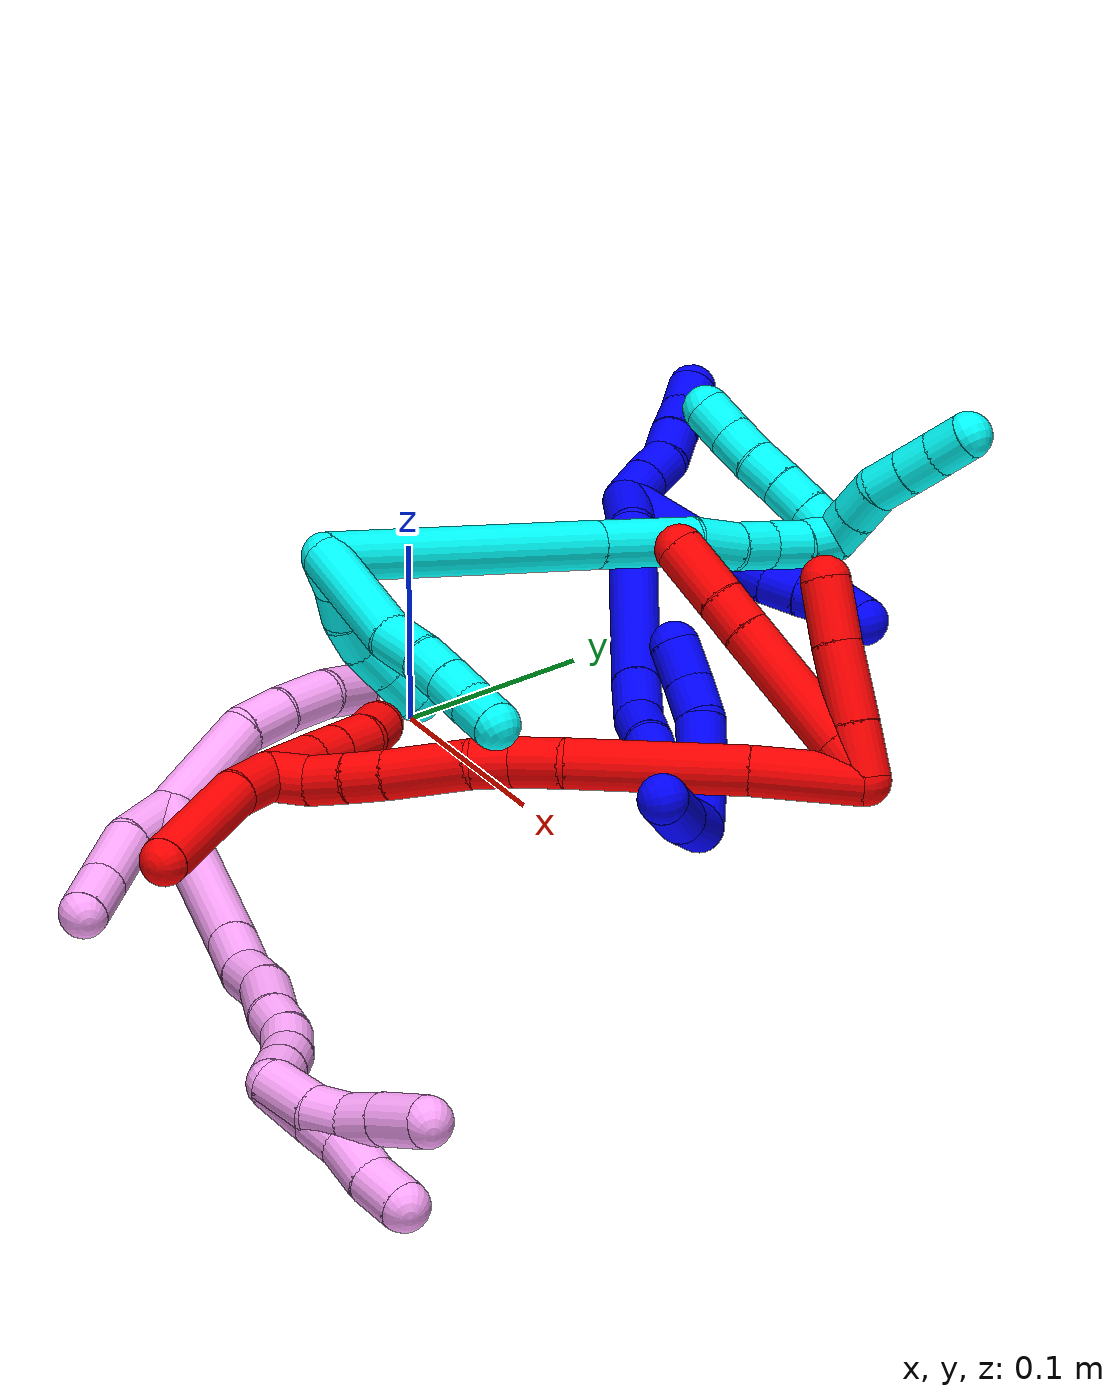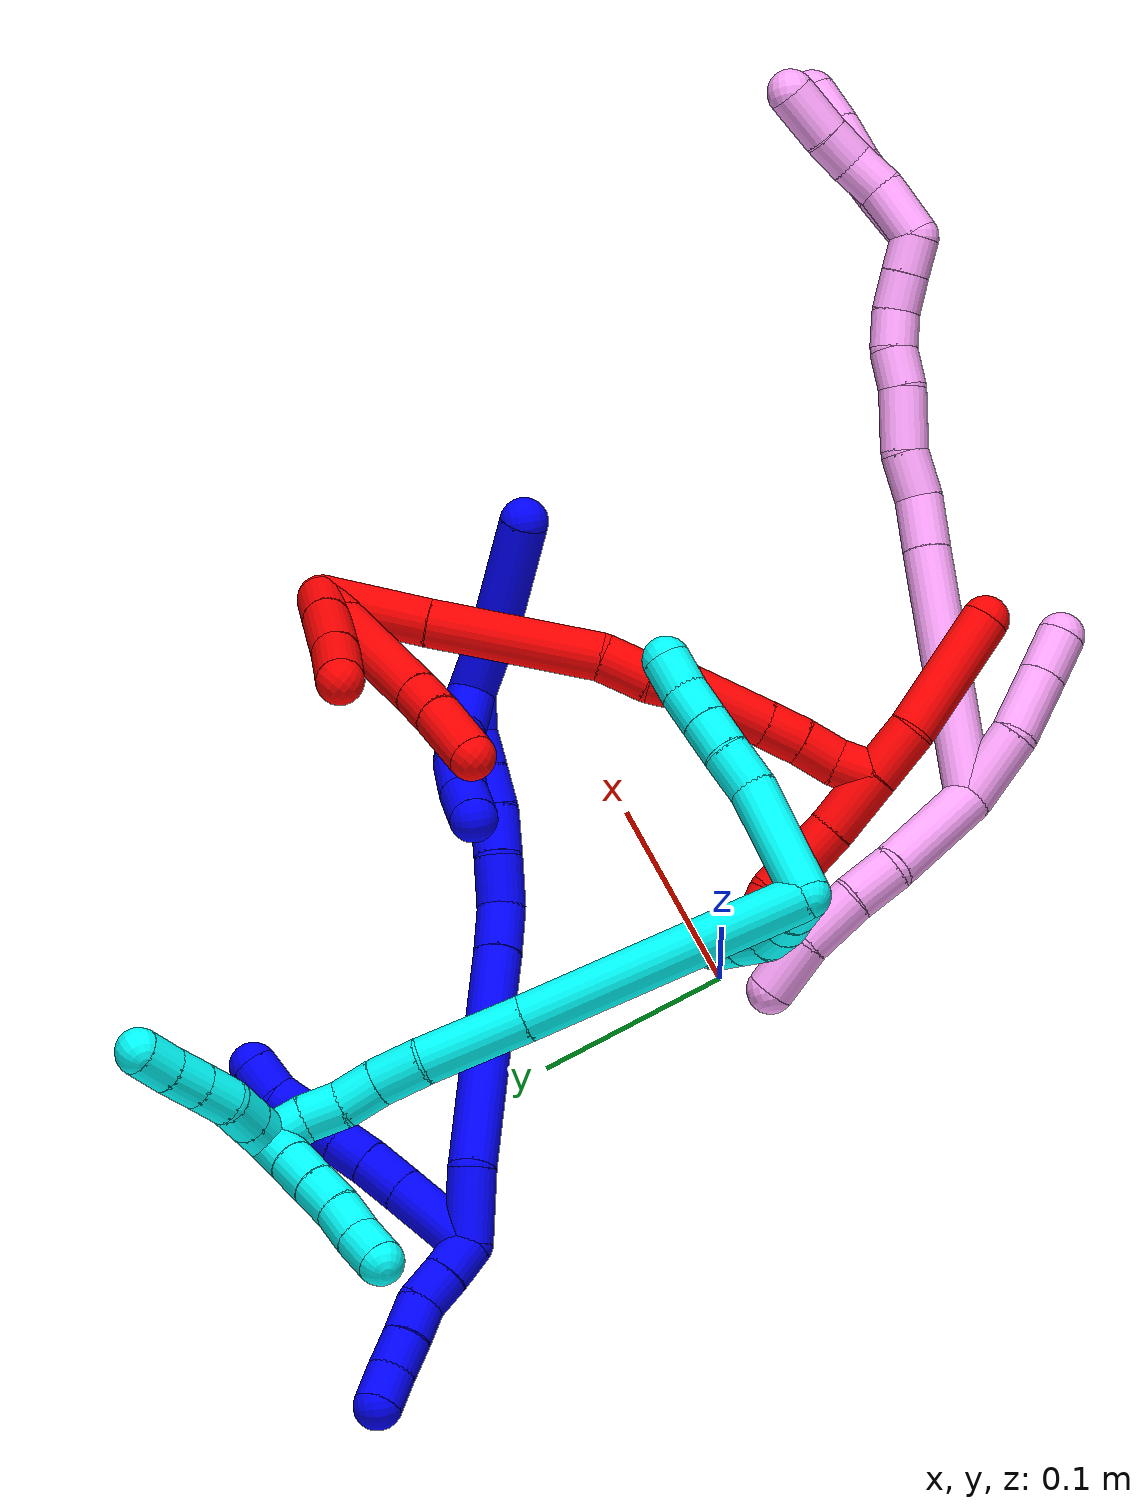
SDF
<sdf version="1.7">
 <world name="default">
  <plugin name="TubeGeneratorPlugin" filename="libtube_generator_plugin.so"/>
  <model name="photoneo_s_sensor">
   <static>1</static>
   <pose>0 0 2 1.57079 1.57079 3.14159</pose>
   <link name="link">
    <inertial><mass>0.1</mass></inertial>
    <sensor name="sensor" type="depth">
     <update_rate>30</update_rate>
     <camera>
      <horizontal_fov>1.22</horizontal_fov>
      <image><width>1920</width><height>1200</height><format>B8G8R8</format></image>
      <clip><near>0.1</near><far>4</far></clip>
      <depth_camera><output>points</output></depth_camera>
     </camera>
     <plugin name="camera_plugin" filename="libgazebo_ros_depth_camera.so">
      <baseline>0.2</baseline>
      <alwaysOn>1</alwaysOn>
      <updateRate>0.0</updateRate>
      <cameraName>camera_ir</cameraName>
      <imageTopicName>/camera/color/image_raw</imageTopicName>
      <cameraInfoTopicName>/camera/color/camera_info</cameraInfoTopicName>
      <depthImageTopicName>/camera/depth/image_raw</depthImageTopicName>
      <depthImageCameraInfoTopicName>/camera/depth/camera_info</depthImageCameraInfoTopicName>
      <pointCloudTopicName>/camera/depth/points</pointCloudTopicName>
      <frameName>fr_optical</frameName>
      <pointCloudCutoff>0.1</pointCloudCutoff>
      <pointCloudCutoffMax>2.0</pointCloudCutoffMax>
      <distortionK1>0</distortionK1>
      <distortionK2>0</distortionK2>
      <distortionK3>0</distortionK3>
      <distortionT1>0</distortionT1>
      <distortionT2>0</distortionT2>
      <CxPrime>0</CxPrime>
      <Cx>0</Cx>
      <Cy>0</Cy>
      <focalLength>0</focalLength>
      <hackBaseline>0</hackBaseline>
     </plugin>
    </sensor>
   </link>
  </model>
  <gravity>0 0 -9.8</gravity>
  <magnetic_field>6e-06 2.3e-05 -4.2e-05</magnetic_field>
  <atmosphere type="adiabatic"/>
  <physics name="default_physics" default="0" type="ode">
   <max_step_size>0.003</max_step_size>
   <real_time_factor>1</real_time_factor>
   <real_time_update_rate>1000</real_time_update_rate>
   <max_contacts>10000</max_contacts>
   <ode>
    <solver>
     <type>quick</type>
     <iters>100</iters>
     <sor>1.3</sor>
     <use_dynamic_moi_rescaling>0</use_dynamic_moi_rescaling>
    </solver>
    <constraints>
     <contact_max_correcting_vel>0</contact_max_correcting_vel>
     <contact_surface_layer>0.001</contact_surface_layer>
     <cfm>0</cfm>
     <erp>0.2</erp>
    </constraints>
   </ode>
  </physics>
  <scene><ambient>0.4 0.4 0.4 1</ambient><background>0.7 0.7 0.7 1</background><shadows>0</shadows></scene>
  <audio><device>default</device></audio>
  <spherical_coordinates>
   <surface_model>EARTH_WGS84</surface_model>
   <latitude_deg>0</latitude_deg>
   <longitude_deg>0</longitude_deg>
   <elevation>0</elevation>
   <heading_deg>0</heading_deg>
  </spherical_coordinates>
  <model name="bin">
   <static>1</static>
   <link name="bottom">
    <collision name="collision-bottom">
     <pose>0 0 -0.01 0 -0 0</pose>
     <geometry><box><size>0.8 0.6 0.02</size></box></geometry>
     <surface>
      <friction><ode><mu>100</mu><mu2>100</mu2></ode></friction>
      <contact><collide_bitmask>65535</collide_bitmask></contact>
     </surface>
    </collision>
   </link>
   <link name="west_wall">
    <collision name="collision-west_wall">
     <pose>-0.41 0 0.1 0 -0 0</pose>
     <geometry><box><size>0.02 0.6 0.2</size></box></geometry>
     <surface>
      <friction><ode><mu>100</mu><mu2>100</mu2></ode></friction>
      <contact><collide_bitmask>65535</collide_bitmask></contact>
     </surface>
    </collision>
   </link>
   <link name="east_wall">
    <collision name="collision-east_wall">
     <pose>0.41 0 0.1 0 -0 0</pose>
     <geometry><box><size>0.02 0.6 0.2</size></box></geometry>
     <surface>
      <friction><ode><mu>100</mu><mu2>100</mu2></ode></friction>
      <contact><collide_bitmask>65535</collide_bitmask></contact>
     </surface>
    </collision>
   </link>
   <link name="south_wall">
    <collision name="collision-south_wall">
     <pose>0 -0.31 0.1 0 -0 0</pose>
     <geometry><box><size>0.8 0.02 0.2</size></box></geometry>
     <surface>
      <friction><ode><mu>100</mu><mu2>100</mu2></ode></friction>
      <contact><collide_bitmask>65535</collide_bitmask></contact>
     </surface>
    </collision>
   </link>
   <link name="north_wall">
    <collision name="collision-north_wall">
     <pose>0 0.31 0.1 0 -0 0</pose>
     <geometry><box><size>0.8 0.02 0.2</size></box></geometry>
     <surface>
      <friction><ode><mu>100</mu><mu2>100</mu2></ode></friction>
      <contact><collide_bitmask>65535</collide_bitmask></contact>
     </surface>
    </collision>
   </link>
  </model>
  <model name="1">
   <static>0</static>
   <link name="1">
    <collision name="collision-cylinder-e_1_2_8">
     <pose>0.018285 -0.004562 0.013259 0.331347 0.916598 0.164604</pose>
     <geometry><cylinder><radius>0.0125</radius><length>0.046086</length></cylinder></geometry>
     <surface>
      <friction><ode><mu>1.16</mu><mu2>1.16</mu2><slip1>0</slip1><slip2>0</slip2></ode></friction>
      <contact><ode><kp>1e+06</kp><kd>1</kd><max_vel>0</max_vel><min_depth>0.001</min_depth></ode></contact>
     </surface>
    </collision>
    <visual name="visual-cylinder-e_1_2_8">
     <pose>0.018285 -0.004562 0.013259 0.331347 0.916598 0.164604</pose>
     <geometry><cylinder><radius>0.0125</radius><length>0.046086</length></cylinder></geometry>
     <material><ambient>0 0 1 1</ambient></material>
    </visual>
    <collision name="collision-cylinder-e_2_8_9">
     <pose>0.045738 -0.011866 0.033627 0.368183 0.877341 0.174272</pose>
     <geometry><cylinder><radius>0.0125</radius><length>0.023839</length></cylinder></geometry>
     <surface>
      <friction><ode><mu>1.16</mu><mu2>1.16</mu2><slip1>0</slip1><slip2>0</slip2></ode></friction>
      <contact><ode><kp>1e+06</kp><kd>1</kd><max_vel>0</max_vel><min_depth>0.001</min_depth></ode></contact>
     </surface>
    </collision>
    <visual name="visual-cylinder-e_2_8_9">
     <pose>0.045738 -0.011866 0.033627 0.368183 0.877341 0.174272</pose>
     <geometry><cylinder><radius>0.0125</radius><length>0.023839</length></cylinder></geometry>
     <material><ambient>0 0 1 1</ambient></material>
    </visual>
    <collision name="collision-cylinder-e_3_9_10">
     <pose>0.062255 -0.016581 0.047234 0.294807 0.82491 0.129754</pose>
     <geometry><cylinder><radius>0.0125</radius><length>0.020015</length></cylinder></geometry>
     <surface>
      <friction><ode><mu>1.16</mu><mu2>1.16</mu2><slip1>0</slip1><slip2>0</slip2></ode></friction>
      <contact><ode><kp>1e+06</kp><kd>1</kd><max_vel>0</max_vel><min_depth>0.001</min_depth></ode></contact>
     </surface>
    </collision>
    <visual name="visual-cylinder-e_3_9_10">
     <pose>0.062255 -0.016581 0.047234 0.294807 0.82491 0.129754</pose>
     <geometry><cylinder><radius>0.0125</radius><length>0.020015</length></cylinder></geometry>
     <material><ambient>0 0 1 1</ambient></material>
    </visual>
    <collision name="collision-cylinder-e_4_10_11">
     <pose>0.076411 -0.021753 0.060349 0.450277 0.747105 0.179052</pose>
     <geometry><cylinder><radius>0.0125</radius><length>0.020032</length></cylinder></geometry>
     <surface>
      <friction><ode><mu>1.16</mu><mu2>1.16</mu2><slip1>0</slip1><slip2>0</slip2></ode></friction>
      <contact><ode><kp>1e+06</kp><kd>1</kd><max_vel>0</max_vel><min_depth>0.001</min_depth></ode></contact>
     </surface>
    </collision>
    <visual name="visual-cylinder-e_4_10_11">
     <pose>0.076411 -0.021753 0.060349 0.450277 0.747105 0.179052</pose>
     <geometry><cylinder><radius>0.0125</radius><length>0.020032</length></cylinder></geometry>
     <material><ambient>0 0 1 1</ambient></material>
    </visual>
    <collision name="collision-cylinder-e_5_11_12">
     <pose>0.089646 -0.028116 0.073949 0.42548 0.697694 0.156812</pose>
     <geometry><cylinder><radius>0.0125</radius><length>0.020013</length></cylinder></geometry>
     <surface>
      <friction><ode><mu>1.16</mu><mu2>1.16</mu2><slip1>0</slip1><slip2>0</slip2></ode></friction>
      <contact><ode><kp>1e+06</kp><kd>1</kd><max_vel>0</max_vel><min_depth>0.001</min_depth></ode></contact>
     </surface>
    </collision>
    <visual name="visual-cylinder-e_5_11_12">
     <pose>0.089646 -0.028116 0.073949 0.42548 0.697694 0.156812</pose>
     <geometry><cylinder><radius>0.0125</radius><length>0.020013</length></cylinder></geometry>
     <material><ambient>0 0 1 1</ambient></material>
    </visual>
    <collision name="collision-cylinder-e_6_12_6">
     <pose>0.104292 -0.035105 0.085176 0.733519 0.96338 0.396355</pose>
     <geometry><cylinder><radius>0.0125</radius><length>0.020014</length></cylinder></geometry>
     <surface>
      <friction><ode><mu>1.16</mu><mu2>1.16</mu2><slip1>0</slip1><slip2>0</slip2></ode></friction>
      <contact><ode><kp>1e+06</kp><kd>1</kd><max_vel>0</max_vel><min_depth>0.001</min_depth></ode></contact>
     </surface>
    </collision>
    <visual name="visual-cylinder-e_6_12_6">
     <pose>0.104292 -0.035105 0.085176 0.733519 0.96338 0.396355</pose>
     <geometry><cylinder><radius>0.0125</radius><length>0.020014</length></cylinder></geometry>
     <material><ambient>0 0 1 1</ambient></material>
    </visual>
    <collision name="collision-cylinder-e_1_2_13">
     <pose>-0.006223 0.003249 0.007121 -0.428054 -0.6717 0.151457</pose>
     <geometry><cylinder><radius>0.0125</radius><length>0.02</length></cylinder></geometry>
     <surface>
      <friction><ode><mu>1.16</mu><mu2>1.16</mu2><slip1>0</slip1><slip2>0</slip2></ode></friction>
      <contact><ode><kp>1e+06</kp><kd>1</kd><max_vel>0</max_vel><min_depth>0.001</min_depth></ode></contact>
     </surface>
    </collision>
    <visual name="visual-cylinder-e_1_2_13">
     <pose>-0.006223 0.003249 0.007121 -0.428054 -0.6717 0.151457</pose>
     <geometry><cylinder><radius>0.0125</radius><length>0.02</length></cylinder></geometry>
     <material><ambient>0 0 1 1</ambient></material>
    </visual>
    <collision name="collision-cylinder-e_2_13_14">
     <pose>-0.018227 0.009678 0.021757 -0.400303 -0.616408 0.128986</pose>
     <geometry><cylinder><radius>0.0125</radius><length>0.02</length></cylinder></geometry>
     <surface>
      <friction><ode><mu>1.16</mu><mu2>1.16</mu2><slip1>0</slip1><slip2>0</slip2></ode></friction>
      <contact><ode><kp>1e+06</kp><kd>1</kd><max_vel>0</max_vel><min_depth>0.001</min_depth></ode></contact>
     </surface>
    </collision>
    <visual name="visual-cylinder-e_2_13_14">
     <pose>-0.018227 0.009678 0.021757 -0.400303 -0.616408 0.128986</pose>
     <geometry><cylinder><radius>0.0125</radius><length>0.02</length></cylinder></geometry>
     <material><ambient>0 0 1 1</ambient></material>
    </visual>
    <collision name="collision-cylinder-e_3_14_15">
     <pose>-0.032004 0.016127 0.034311 -0.575507 -0.926501 0.293548</pose>
     <geometry><cylinder><radius>0.0125</radius><length>0.02</length></cylinder></geometry>
     <surface>
      <friction><ode><mu>1.16</mu><mu2>1.16</mu2><slip1>0</slip1><slip2>0</slip2></ode></friction>
      <contact><ode><kp>1e+06</kp><kd>1</kd><max_vel>0</max_vel><min_depth>0.001</min_depth></ode></contact>
     </surface>
    </collision>
    <visual name="visual-cylinder-e_3_14_15">
     <pose>-0.032004 0.016127 0.034311 -0.575507 -0.926501 0.293548</pose>
     <geometry><cylinder><radius>0.0125</radius><length>0.02</length></cylinder></geometry>
     <material><ambient>0 0 1 1</ambient></material>
    </visual>
    <collision name="collision-cylinder-e_4_15_16">
     <pose>-0.047519 0.023179 0.044747 -0.611269 -0.851113 0.284095</pose>
     <geometry><cylinder><radius>0.0125</radius><length>0.02</length></cylinder></geometry>
     <surface>
      <friction><ode><mu>1.16</mu><mu2>1.16</mu2><slip1>0</slip1><slip2>0</slip2></ode></friction>
      <contact><ode><kp>1e+06</kp><kd>1</kd><max_vel>0</max_vel><min_depth>0.001</min_depth></ode></contact>
     </surface>
    </collision>
    <visual name="visual-cylinder-e_4_15_16">
     <pose>-0.047519 0.023179 0.044747 -0.611269 -0.851113 0.284095</pose>
     <geometry><cylinder><radius>0.0125</radius><length>0.02</length></cylinder></geometry>
     <material><ambient>0 0 1 1</ambient></material>
    </visual>
    <collision name="collision-cylinder-e_5_16_5">
     <pose>-0.063143 0.029993 0.05516 -0.543678 -0.944721 0.282935</pose>
     <geometry><cylinder><radius>0.0125</radius><length>0.02</length></cylinder></geometry>
     <surface>
      <friction><ode><mu>1.16</mu><mu2>1.16</mu2><slip1>0</slip1><slip2>0</slip2></ode></friction>
      <contact><ode><kp>1e+06</kp><kd>1</kd><max_vel>0</max_vel><min_depth>0.001</min_depth></ode></contact>
     </surface>
    </collision>
    <visual name="visual-cylinder-e_5_16_5">
     <pose>-0.063143 0.029993 0.05516 -0.543678 -0.944721 0.282935</pose>
     <geometry><cylinder><radius>0.0125</radius><length>0.02</length></cylinder></geometry>
     <material><ambient>0 0 1 1</ambient></material>
    </visual>
    <collision name="collision-cylinder-e_1_2_17">
     <pose>0.014038 -0.012541 -0.003919 1.87367 0.818494 1.066</pose>
     <geometry><cylinder><radius>0.0125</radius><length>0.038455</length></cylinder></geometry>
     <surface>
      <friction><ode><mu>1.16</mu><mu2>1.16</mu2><slip1>0</slip1><slip2>0</slip2></ode></friction>
      <contact><ode><kp>1e+06</kp><kd>1</kd><max_vel>0</max_vel><min_depth>0.001</min_depth></ode></contact>
     </surface>
    </collision>
    <visual name="visual-cylinder-e_1_2_17">
     <pose>0.014038 -0.012541 -0.003919 1.87367 0.818494 1.066</pose>
     <geometry><cylinder><radius>0.0125</radius><length>0.038455</length></cylinder></geometry>
     <material><ambient>0 0 1 1</ambient></material>
    </visual>
    <collision name="collision-cylinder-e_2_17_18">
     <pose>0.08086 -0.048152 -0.024763 2.20374 1.07404 1.73157</pose>
     <geometry><cylinder><radius>0.0125</radius><length>0.120079</length></cylinder></geometry>
     <surface>
      <friction><ode><mu>1.16</mu><mu2>1.16</mu2><slip1>0</slip1><slip2>0</slip2></ode></friction>
      <contact><ode><kp>1e+06</kp><kd>1</kd><max_vel>0</max_vel><min_depth>0.001</min_depth></ode></contact>
     </surface>
    </collision>
    <visual name="visual-cylinder-e_2_17_18">
     <pose>0.08086 -0.048152 -0.024763 2.20374 1.07404 1.73157</pose>
     <geometry><cylinder><radius>0.0125</radius><length>0.120079</length></cylinder></geometry>
     <material><ambient>0 0 1 1</ambient></material>
    </visual>
    <collision name="collision-cylinder-e_3_18_19">
     <pose>0.145343 -0.075996 -0.044959 2.17149 1.11147 1.73414</pose>
     <geometry><cylinder><radius>0.0125</radius><length>0.026107</length></cylinder></geometry>
     <surface>
      <friction><ode><mu>1.16</mu><mu2>1.16</mu2><slip1>0</slip1><slip2>0</slip2></ode></friction>
      <contact><ode><kp>1e+06</kp><kd>1</kd><max_vel>0</max_vel><min_depth>0.001</min_depth></ode></contact>
     </surface>
    </collision>
    <visual name="visual-cylinder-e_3_18_19">
     <pose>0.145343 -0.075996 -0.044959 2.17149 1.11147 1.73414</pose>
     <geometry><cylinder><radius>0.0125</radius><length>0.026107</length></cylinder></geometry>
     <material><ambient>0 0 1 1</ambient></material>
    </visual>
    <collision name="collision-cylinder-e_4_19_20">
     <pose>0.167164 -0.089293 -0.04955 1.7245 0.865046 0.988274</pose>
     <geometry><cylinder><radius>0.0125</radius><length>0.026593</length></cylinder></geometry>
     <surface>
      <friction><ode><mu>1.16</mu><mu2>1.16</mu2><slip1>0</slip1><slip2>0</slip2></ode></friction>
      <contact><ode><kp>1e+06</kp><kd>1</kd><max_vel>0</max_vel><min_depth>0.001</min_depth></ode></contact>
     </surface>
    </collision>
    <visual name="visual-cylinder-e_4_19_20">
     <pose>0.167164 -0.089293 -0.04955 1.7245 0.865046 0.988274</pose>
     <geometry><cylinder><radius>0.0125</radius><length>0.026593</length></cylinder></geometry>
     <material><ambient>0 0 1 1</ambient></material>
    </visual>
    <collision name="collision-cylinder-e_5_20_21">
     <pose>0.188388 -0.103812 -0.052154 1.78159 1.06619 1.26077</pose>
     <geometry><cylinder><radius>0.0125</radius><length>0.025369</length></cylinder></geometry>
     <surface>
      <friction><ode><mu>1.16</mu><mu2>1.16</mu2><slip1>0</slip1><slip2>0</slip2></ode></friction>
      <contact><ode><kp>1e+06</kp><kd>1</kd><max_vel>0</max_vel><min_depth>0.001</min_depth></ode></contact>
     </surface>
    </collision>
    <visual name="visual-cylinder-e_5_20_21">
     <pose>0.188388 -0.103812 -0.052154 1.78159 1.06619 1.26077</pose>
     <geometry><cylinder><radius>0.0125</radius><length>0.025369</length></cylinder></geometry>
     <material><ambient>0 0 1 1</ambient></material>
    </visual>
    <collision name="collision-cylinder-e_6_21_22">
     <pose>0.208928 -0.115186 -0.052603 1.41685 1.04772 0.919226</pose>
     <geometry><cylinder><radius>0.0125</radius><length>0.021785</length></cylinder></geometry>
     <surface>
      <friction><ode><mu>1.16</mu><mu2>1.16</mu2><slip1>0</slip1><slip2>0</slip2></ode></friction>
      <contact><ode><kp>1e+06</kp><kd>1</kd><max_vel>0</max_vel><min_depth>0.001</min_depth></ode></contact>
     </surface>
    </collision>
    <visual name="visual-cylinder-e_6_21_22">
     <pose>0.208928 -0.115186 -0.052603 1.41685 1.04772 0.919226</pose>
     <geometry><cylinder><radius>0.0125</radius><length>0.021785</length></cylinder></geometry>
     <material><ambient>0 0 1 1</ambient></material>
    </visual>
    <collision name="collision-cylinder-e_7_22_23">
     <pose>0.226777 -0.126529 -0.050763 1.40392 0.947376 0.818079</pose>
     <geometry><cylinder><radius>0.0125</radius><length>0.020725</length></cylinder></geometry>
     <surface>
      <friction><ode><mu>1.16</mu><mu2>1.16</mu2><slip1>0</slip1><slip2>0</slip2></ode></friction>
      <contact><ode><kp>1e+06</kp><kd>1</kd><max_vel>0</max_vel><min_depth>0.001</min_depth></ode></contact>
     </surface>
    </collision>
    <visual name="visual-cylinder-e_7_22_23">
     <pose>0.226777 -0.126529 -0.050763 1.40392 0.947376 0.818079</pose>
     <geometry><cylinder><radius>0.0125</radius><length>0.020725</length></cylinder></geometry>
     <material><ambient>0 0 1 1</ambient></material>
    </visual>
    <collision name="collision-cylinder-e_8_23_1">
     <pose>0.242009 -0.140344 -0.050727 1.69358 0.711471 0.795616</pose>
     <geometry><cylinder><radius>0.0125</radius><length>0.020886</length></cylinder></geometry>
     <surface>
      <friction><ode><mu>1.16</mu><mu2>1.16</mu2><slip1>0</slip1><slip2>0</slip2></ode></friction>
      <contact><ode><kp>1e+06</kp><kd>1</kd><max_vel>0</max_vel><min_depth>0.001</min_depth></ode></contact>
     </surface>
    </collision>
    <visual name="visual-cylinder-e_8_23_1">
     <pose>0.242009 -0.140344 -0.050727 1.69358 0.711471 0.795616</pose>
     <geometry><cylinder><radius>0.0125</radius><length>0.020886</length></cylinder></geometry>
     <material><ambient>0 0 1 1</ambient></material>
    </visual>
    <collision name="collision-cylinder-e_1_1_24">
     <pose>0.233961 -0.148353 -0.046383 0.029742 -1.22741 -0.020952</pose>
     <geometry><cylinder><radius>0.0125</radius><length>0.031577</length></cylinder></geometry>
     <surface>
      <friction><ode><mu>1.16</mu><mu2>1.16</mu2><slip1>0</slip1><slip2>0</slip2></ode></friction>
      <contact><ode><kp>1e+06</kp><kd>1</kd><max_vel>0</max_vel><min_depth>0.001</min_depth></ode></contact>
     </surface>
    </collision>
    <visual name="visual-cylinder-e_1_1_24">
     <pose>0.233961 -0.148353 -0.046383 0.029742 -1.22741 -0.020952</pose>
     <geometry><cylinder><radius>0.0125</radius><length>0.031577</length></cylinder></geometry>
     <material><ambient>0 0 1 1</ambient></material>
    </visual>
    <collision name="collision-cylinder-e_2_24_25">
     <pose>0.20658 -0.149395 -0.037879 0.270236 -1.31214 -0.208551</pose>
     <geometry><cylinder><radius>0.0125</radius><length>0.025889</length></cylinder></geometry>
     <surface>
      <friction><ode><mu>1.16</mu><mu2>1.16</mu2><slip1>0</slip1><slip2>0</slip2></ode></friction>
      <contact><ode><kp>1e+06</kp><kd>1</kd><max_vel>0</max_vel><min_depth>0.001</min_depth></ode></contact>
     </surface>
    </collision>
    <visual name="visual-cylinder-e_2_24_25">
     <pose>0.20658 -0.149395 -0.037879 0.270236 -1.31214 -0.208551</pose>
     <geometry><cylinder><radius>0.0125</radius><length>0.025889</length></cylinder></geometry>
     <material><ambient>0 0 1 1</ambient></material>
    </visual>
    <collision name="collision-cylinder-e_3_25_26">
     <pose>0.183846 -0.148785 -0.034416 -1.39106 -1.42332 1.24783</pose>
     <geometry><cylinder><radius>0.0125</radius><length>0.020663</length></cylinder></geometry>
     <surface>
      <friction><ode><mu>1.16</mu><mu2>1.16</mu2><slip1>0</slip1><slip2>0</slip2></ode></friction>
      <contact><ode><kp>1e+06</kp><kd>1</kd><max_vel>0</max_vel><min_depth>0.001</min_depth></ode></contact>
     </surface>
    </collision>
    <visual name="visual-cylinder-e_3_25_26">
     <pose>0.183846 -0.148785 -0.034416 -1.39106 -1.42332 1.24783</pose>
     <geometry><cylinder><radius>0.0125</radius><length>0.020663</length></cylinder></geometry>
     <material><ambient>0 0 1 1</ambient></material>
    </visual>
    <collision name="collision-cylinder-e_4_26_4">
     <pose>0.162735 -0.148077 -0.034719 2.20127 -1.48171 -2.12736</pose>
     <geometry><cylinder><radius>0.0125</radius><length>0.02187</length></cylinder></geometry>
     <surface>
      <friction><ode><mu>1.16</mu><mu2>1.16</mu2><slip1>0</slip1><slip2>0</slip2></ode></friction>
      <contact><ode><kp>1e+06</kp><kd>1</kd><max_vel>0</max_vel><min_depth>0.001</min_depth></ode></contact>
     </surface>
    </collision>
    <visual name="visual-cylinder-e_4_26_4">
     <pose>0.162735 -0.148077 -0.034719 2.20127 -1.48171 -2.12736</pose>
     <geometry><cylinder><radius>0.0125</radius><length>0.02187</length></cylinder></geometry>
     <material><ambient>0 0 1 1</ambient></material>
    </visual>
    <collision name="collision-cylinder-e_1_1_27">
     <pose>0.253041 -0.166301 -0.059658 1.9851 0.209856 0.319965</pose>
     <geometry><cylinder><radius>0.0125</radius><length>0.040446</length></cylinder></geometry>
     <surface>
      <friction><ode><mu>1.16</mu><mu2>1.16</mu2><slip1>0</slip1><slip2>0</slip2></ode></friction>
      <contact><ode><kp>1e+06</kp><kd>1</kd><max_vel>0</max_vel><min_depth>0.001</min_depth></ode></contact>
     </surface>
    </collision>
    <visual name="visual-cylinder-e_1_1_27">
     <pose>0.253041 -0.166301 -0.059658 1.9851 0.209856 0.319965</pose>
     <geometry><cylinder><radius>0.0125</radius><length>0.040446</length></cylinder></geometry>
     <material><ambient>0 0 1 1</ambient></material>
    </visual>
    <collision name="collision-cylinder-e_2_27_3">
     <pose>0.263056 -0.212146 -0.076761 1.8891 0.196115 0.270324</pose>
     <geometry><cylinder><radius>0.0125</radius><length>0.059554</length></cylinder></geometry>
     <surface>
      <friction><ode><mu>1.16</mu><mu2>1.16</mu2><slip1>0</slip1><slip2>0</slip2></ode></friction>
      <contact><ode><kp>1e+06</kp><kd>1</kd><max_vel>0</max_vel><min_depth>0.001</min_depth></ode></contact>
     </surface>
    </collision>
    <visual name="visual-cylinder-e_2_27_3">
     <pose>0.263056 -0.212146 -0.076761 1.8891 0.196115 0.270324</pose>
     <geometry><cylinder><radius>0.0125</radius><length>0.059554</length></cylinder></geometry>
     <material><ambient>0 0 1 1</ambient></material>
    </visual>
    <collision name="collision-sphere-3">
     <pose>0.268858 -0.239885 -0.085901 0 -0 0</pose>
     <geometry><sphere><radius>0.0125</radius></sphere></geometry>
     <surface>
      <friction><ode><mu>1.16</mu><mu2>1.16</mu2><slip1>0</slip1><slip2>0</slip2></ode></friction>
      <contact><ode><kp>1e+06</kp><kd>1</kd><max_vel>0</max_vel><min_depth>0.001</min_depth></ode></contact>
     </surface>
    </collision>
    <visual name="visual-sphere-3">
     <pose>0.268858 -0.239885 -0.085901 0 -0 0</pose>
     <geometry><sphere><radius>0.0125</radius></sphere></geometry>
     <material><ambient>0 0 1 1</ambient></material>
    </visual>
    <collision name="collision-sphere-27">
     <pose>0.257254 -0.184407 -0.067621 0 -0 0</pose>
     <geometry><sphere><radius>0.0125</radius></sphere></geometry>
     <surface>
      <friction><ode><mu>1.16</mu><mu2>1.16</mu2><slip1>0</slip1><slip2>0</slip2></ode></friction>
      <contact><ode><kp>1e+06</kp><kd>1</kd><max_vel>0</max_vel><min_depth>0.001</min_depth></ode></contact>
     </surface>
    </collision>
    <visual name="visual-sphere-27">
     <pose>0.257254 -0.184407 -0.067621 0 -0 0</pose>
     <geometry><sphere><radius>0.0125</radius></sphere></geometry>
     <material><ambient>0 0 1 1</ambient></material>
    </visual>
    <collision name="collision-sphere-4">
     <pose>0.151844 -0.148863 -0.035292 0 -0 0</pose>
     <geometry><sphere><radius>0.0125</radius></sphere></geometry>
     <surface>
      <friction><ode><mu>1.16</mu><mu2>1.16</mu2><slip1>0</slip1><slip2>0</slip2></ode></friction>
      <contact><ode><kp>1e+06</kp><kd>1</kd><max_vel>0</max_vel><min_depth>0.001</min_depth></ode></contact>
     </surface>
    </collision>
    <visual name="visual-sphere-4">
     <pose>0.151844 -0.148863 -0.035292 0 -0 0</pose>
     <geometry><sphere><radius>0.0125</radius></sphere></geometry>
     <material><ambient>0 0 1 1</ambient></material>
    </visual>
    <collision name="collision-sphere-26">
     <pose>0.173627 -0.147291 -0.034145 0 -0 0</pose>
     <geometry><sphere><radius>0.0125</radius></sphere></geometry>
     <surface>
      <friction><ode><mu>1.16</mu><mu2>1.16</mu2><slip1>0</slip1><slip2>0</slip2></ode></friction>
      <contact><ode><kp>1e+06</kp><kd>1</kd><max_vel>0</max_vel><min_depth>0.001</min_depth></ode></contact>
     </surface>
    </collision>
    <visual name="visual-sphere-26">
     <pose>0.173627 -0.147291 -0.034145 0 -0 0</pose>
     <geometry><sphere><radius>0.0125</radius></sphere></geometry>
     <material><ambient>0 0 1 1</ambient></material>
    </visual>
    <collision name="collision-sphere-25">
     <pose>0.194066 -0.150278 -0.034688 0 -0 0</pose>
     <geometry><sphere><radius>0.0125</radius></sphere></geometry>
     <surface>
      <friction><ode><mu>1.16</mu><mu2>1.16</mu2><slip1>0</slip1><slip2>0</slip2></ode></friction>
      <contact><ode><kp>1e+06</kp><kd>1</kd><max_vel>0</max_vel><min_depth>0.001</min_depth></ode></contact>
     </surface>
    </collision>
    <visual name="visual-sphere-25">
     <pose>0.194066 -0.150278 -0.034688 0 -0 0</pose>
     <geometry><sphere><radius>0.0125</radius></sphere></geometry>
     <material><ambient>0 0 1 1</ambient></material>
    </visual>
    <collision name="collision-sphere-24">
     <pose>0.219094 -0.148511 -0.04107 0 -0 0</pose>
     <geometry><sphere><radius>0.0125</radius></sphere></geometry>
     <surface>
      <friction><ode><mu>1.16</mu><mu2>1.16</mu2><slip1>0</slip1><slip2>0</slip2></ode></friction>
      <contact><ode><kp>1e+06</kp><kd>1</kd><max_vel>0</max_vel><min_depth>0.001</min_depth></ode></contact>
     </surface>
    </collision>
    <visual name="visual-sphere-24">
     <pose>0.219094 -0.148511 -0.04107 0 -0 0</pose>
     <geometry><sphere><radius>0.0125</radius></sphere></geometry>
     <material><ambient>0 0 1 1</ambient></material>
    </visual>
    <collision name="collision-sphere-1">
     <pose>0.248828 -0.148195 -0.051696 0 -0 0</pose>
     <geometry><sphere><radius>0.0125</radius></sphere></geometry>
     <surface>
      <friction><ode><mu>1.16</mu><mu2>1.16</mu2><slip1>0</slip1><slip2>0</slip2></ode></friction>
      <contact><ode><kp>1e+06</kp><kd>1</kd><max_vel>0</max_vel><min_depth>0.001</min_depth></ode></contact>
     </surface>
    </collision>
    <visual name="visual-sphere-1">
     <pose>0.248828 -0.148195 -0.051696 0 -0 0</pose>
     <geometry><sphere><radius>0.0125</radius></sphere></geometry>
     <material><ambient>0 0 1 1</ambient></material>
    </visual>
    <collision name="collision-sphere-23">
     <pose>0.23519 -0.132494 -0.049759 0 -0 0</pose>
     <geometry><sphere><radius>0.0125</radius></sphere></geometry>
     <surface>
      <friction><ode><mu>1.16</mu><mu2>1.16</mu2><slip1>0</slip1><slip2>0</slip2></ode></friction>
      <contact><ode><kp>1e+06</kp><kd>1</kd><max_vel>0</max_vel><min_depth>0.001</min_depth></ode></contact>
     </surface>
    </collision>
    <visual name="visual-sphere-23">
     <pose>0.23519 -0.132494 -0.049759 0 -0 0</pose>
     <geometry><sphere><radius>0.0125</radius></sphere></geometry>
     <material><ambient>0 0 1 1</ambient></material>
    </visual>
    <collision name="collision-sphere-22">
     <pose>0.218364 -0.120563 -0.051768 0 -0 0</pose>
     <geometry><sphere><radius>0.0125</radius></sphere></geometry>
     <surface>
      <friction><ode><mu>1.16</mu><mu2>1.16</mu2><slip1>0</slip1><slip2>0</slip2></ode></friction>
      <contact><ode><kp>1e+06</kp><kd>1</kd><max_vel>0</max_vel><min_depth>0.001</min_depth></ode></contact>
     </surface>
    </collision>
    <visual name="visual-sphere-22">
     <pose>0.218364 -0.120563 -0.051768 0 -0 0</pose>
     <geometry><sphere><radius>0.0125</radius></sphere></geometry>
     <material><ambient>0 0 1 1</ambient></material>
    </visual>
    <collision name="collision-sphere-21">
     <pose>0.199492 -0.109809 -0.053437 0 -0 0</pose>
     <geometry><sphere><radius>0.0125</radius></sphere></geometry>
     <surface>
      <friction><ode><mu>1.16</mu><mu2>1.16</mu2><slip1>0</slip1><slip2>0</slip2></ode></friction>
      <contact><ode><kp>1e+06</kp><kd>1</kd><max_vel>0</max_vel><min_depth>0.001</min_depth></ode></contact>
     </surface>
    </collision>
    <visual name="visual-sphere-21">
     <pose>0.199492 -0.109809 -0.053437 0 -0 0</pose>
     <geometry><sphere><radius>0.0125</radius></sphere></geometry>
     <material><ambient>0 0 1 1</ambient></material>
    </visual>
    <collision name="collision-sphere-12">
     <pose>0.096075 -0.031281 0.080934 0 -0 0</pose>
     <geometry><sphere><radius>0.0125</radius></sphere></geometry>
     <surface>
      <friction><ode><mu>1.16</mu><mu2>1.16</mu2><slip1>0</slip1><slip2>0</slip2></ode></friction>
      <contact><ode><kp>1e+06</kp><kd>1</kd><max_vel>0</max_vel><min_depth>0.001</min_depth></ode></contact>
     </surface>
    </collision>
    <visual name="visual-sphere-12">
     <pose>0.096075 -0.031281 0.080934 0 -0 0</pose>
     <geometry><sphere><radius>0.0125</radius></sphere></geometry>
     <material><ambient>0 0 1 1</ambient></material>
    </visual>
    <collision name="collision-sphere-11">
     <pose>0.083218 -0.024951 0.066965 0 -0 0</pose>
     <geometry><sphere><radius>0.0125</radius></sphere></geometry>
     <surface>
      <friction><ode><mu>1.16</mu><mu2>1.16</mu2><slip1>0</slip1><slip2>0</slip2></ode></friction>
      <contact><ode><kp>1e+06</kp><kd>1</kd><max_vel>0</max_vel><min_depth>0.001</min_depth></ode></contact>
     </surface>
    </collision>
    <visual name="visual-sphere-11">
     <pose>0.083218 -0.024951 0.066965 0 -0 0</pose>
     <geometry><sphere><radius>0.0125</radius></sphere></geometry>
     <material><ambient>0 0 1 1</ambient></material>
    </visual>
    <collision name="collision-sphere-10">
     <pose>0.069605 -0.018554 0.053733 0 -0 0</pose>
     <geometry><sphere><radius>0.0125</radius></sphere></geometry>
     <surface>
      <friction><ode><mu>1.16</mu><mu2>1.16</mu2><slip1>0</slip1><slip2>0</slip2></ode></friction>
      <contact><ode><kp>1e+06</kp><kd>1</kd><max_vel>0</max_vel><min_depth>0.001</min_depth></ode></contact>
     </surface>
    </collision>
    <visual name="visual-sphere-10">
     <pose>0.069605 -0.018554 0.053733 0 -0 0</pose>
     <geometry><sphere><radius>0.0125</radius></sphere></geometry>
     <material><ambient>0 0 1 1</ambient></material>
    </visual>
    <collision name="collision-sphere-9">
     <pose>0.054904 -0.014608 0.040736 0 -0 0</pose>
     <geometry><sphere><radius>0.0125</radius></sphere></geometry>
     <surface>
      <friction><ode><mu>1.16</mu><mu2>1.16</mu2><slip1>0</slip1><slip2>0</slip2></ode></friction>
      <contact><ode><kp>1e+06</kp><kd>1</kd><max_vel>0</max_vel><min_depth>0.001</min_depth></ode></contact>
     </surface>
    </collision>
    <visual name="visual-sphere-9">
     <pose>0.054904 -0.014608 0.040736 0 -0 0</pose>
     <geometry><sphere><radius>0.0125</radius></sphere></geometry>
     <material><ambient>0 0 1 1</ambient></material>
    </visual>
    <collision name="collision-sphere-2">
     <geometry><sphere><radius>0.0125</radius></sphere></geometry>
     <surface>
      <friction><ode><mu>1.16</mu><mu2>1.16</mu2><slip1>0</slip1><slip2>0</slip2></ode></friction>
      <contact><ode><kp>1e+06</kp><kd>1</kd><max_vel>0</max_vel><min_depth>0.001</min_depth></ode></contact>
     </surface>
    </collision>
    <visual name="visual-sphere-2">
     <geometry><sphere><radius>0.0125</radius></sphere></geometry>
     <material><ambient>0 0 1 1</ambient></material>
    </visual>
    <collision name="collision-sphere-19">
     <pose>0.157044 -0.08077 -0.04823 0 -0 0</pose>
     <geometry><sphere><radius>0.0125</radius></sphere></geometry>
     <surface>
      <friction><ode><mu>1.16</mu><mu2>1.16</mu2><slip1>0</slip1><slip2>0</slip2></ode></friction>
      <contact><ode><kp>1e+06</kp><kd>1</kd><max_vel>0</max_vel><min_depth>0.001</min_depth></ode></contact>
     </surface>
    </collision>
    <visual name="visual-sphere-19">
     <pose>0.157044 -0.08077 -0.04823 0 -0 0</pose>
     <geometry><sphere><radius>0.0125</radius></sphere></geometry>
     <material><ambient>0 0 1 1</ambient></material>
    </visual>
    <collision name="collision-sphere-8">
     <pose>0.036571 -0.009123 0.026519 0 -0 0</pose>
     <geometry><sphere><radius>0.0125</radius></sphere></geometry>
     <surface>
      <friction><ode><mu>1.16</mu><mu2>1.16</mu2><slip1>0</slip1><slip2>0</slip2></ode></friction>
      <contact><ode><kp>1e+06</kp><kd>1</kd><max_vel>0</max_vel><min_depth>0.001</min_depth></ode></contact>
     </surface>
    </collision>
    <visual name="visual-sphere-8">
     <pose>0.036571 -0.009123 0.026519 0 -0 0</pose>
     <geometry><sphere><radius>0.0125</radius></sphere></geometry>
     <material><ambient>0 0 1 1</ambient></material>
    </visual>
    <collision name="collision-sphere-6">
     <pose>0.112509 -0.038928 0.089419 0 -0 0</pose>
     <geometry><sphere><radius>0.0125</radius></sphere></geometry>
     <surface>
      <friction><ode><mu>1.16</mu><mu2>1.16</mu2><slip1>0</slip1><slip2>0</slip2></ode></friction>
      <contact><ode><kp>1e+06</kp><kd>1</kd><max_vel>0</max_vel><min_depth>0.001</min_depth></ode></contact>
     </surface>
    </collision>
    <visual name="visual-sphere-6">
     <pose>0.112509 -0.038928 0.089419 0 -0 0</pose>
     <geometry><sphere><radius>0.0125</radius></sphere></geometry>
     <material><ambient>0 0 1 1</ambient></material>
    </visual>
    <collision name="collision-sphere-13">
     <pose>-0.012446 0.006499 0.014243 0 -0 0</pose>
     <geometry><sphere><radius>0.0125</radius></sphere></geometry>
     <surface>
      <friction><ode><mu>1.16</mu><mu2>1.16</mu2><slip1>0</slip1><slip2>0</slip2></ode></friction>
      <contact><ode><kp>1e+06</kp><kd>1</kd><max_vel>0</max_vel><min_depth>0.001</min_depth></ode></contact>
     </surface>
    </collision>
    <visual name="visual-sphere-13">
     <pose>-0.012446 0.006499 0.014243 0 -0 0</pose>
     <geometry><sphere><radius>0.0125</radius></sphere></geometry>
     <material><ambient>0 0 1 1</ambient></material>
    </visual>
    <collision name="collision-sphere-14">
     <pose>-0.024009 0.012858 0.029272 0 -0 0</pose>
     <geometry><sphere><radius>0.0125</radius></sphere></geometry>
     <surface>
      <friction><ode><mu>1.16</mu><mu2>1.16</mu2><slip1>0</slip1><slip2>0</slip2></ode></friction>
      <contact><ode><kp>1e+06</kp><kd>1</kd><max_vel>0</max_vel><min_depth>0.001</min_depth></ode></contact>
     </surface>
    </collision>
    <visual name="visual-sphere-14">
     <pose>-0.024009 0.012858 0.029272 0 -0 0</pose>
     <geometry><sphere><radius>0.0125</radius></sphere></geometry>
     <material><ambient>0 0 1 1</ambient></material>
    </visual>
    <collision name="collision-sphere-15">
     <pose>-0.039999 0.019396 0.03935 0 -0 0</pose>
     <geometry><sphere><radius>0.0125</radius></sphere></geometry>
     <surface>
      <friction><ode><mu>1.16</mu><mu2>1.16</mu2><slip1>0</slip1><slip2>0</slip2></ode></friction>
      <contact><ode><kp>1e+06</kp><kd>1</kd><max_vel>0</max_vel><min_depth>0.001</min_depth></ode></contact>
     </surface>
    </collision>
    <visual name="visual-sphere-15">
     <pose>-0.039999 0.019396 0.03935 0 -0 0</pose>
     <geometry><sphere><radius>0.0125</radius></sphere></geometry>
     <material><ambient>0 0 1 1</ambient></material>
    </visual>
    <collision name="collision-sphere-16">
     <pose>-0.055039 0.026962 0.050145 0 -0 0</pose>
     <geometry><sphere><radius>0.0125</radius></sphere></geometry>
     <surface>
      <friction><ode><mu>1.16</mu><mu2>1.16</mu2><slip1>0</slip1><slip2>0</slip2></ode></friction>
      <contact><ode><kp>1e+06</kp><kd>1</kd><max_vel>0</max_vel><min_depth>0.001</min_depth></ode></contact>
     </surface>
    </collision>
    <visual name="visual-sphere-16">
     <pose>-0.055039 0.026962 0.050145 0 -0 0</pose>
     <geometry><sphere><radius>0.0125</radius></sphere></geometry>
     <material><ambient>0 0 1 1</ambient></material>
    </visual>
    <collision name="collision-sphere-5">
     <pose>-0.071246 0.033024 0.060175 0 -0 0</pose>
     <geometry><sphere><radius>0.0125</radius></sphere></geometry>
     <surface>
      <friction><ode><mu>1.16</mu><mu2>1.16</mu2><slip1>0</slip1><slip2>0</slip2></ode></friction>
      <contact><ode><kp>1e+06</kp><kd>1</kd><max_vel>0</max_vel><min_depth>0.001</min_depth></ode></contact>
     </surface>
    </collision>
    <visual name="visual-sphere-5">
     <pose>-0.071246 0.033024 0.060175 0 -0 0</pose>
     <geometry><sphere><radius>0.0125</radius></sphere></geometry>
     <material><ambient>0 0 1 1</ambient></material>
    </visual>
    <collision name="collision-sphere-17">
     <pose>0.028077 -0.025081 -0.007838 0 -0 0</pose>
     <geometry><sphere><radius>0.0125</radius></sphere></geometry>
     <surface>
      <friction><ode><mu>1.16</mu><mu2>1.16</mu2><slip1>0</slip1><slip2>0</slip2></ode></friction>
      <contact><ode><kp>1e+06</kp><kd>1</kd><max_vel>0</max_vel><min_depth>0.001</min_depth></ode></contact>
     </surface>
    </collision>
    <visual name="visual-sphere-17">
     <pose>0.028077 -0.025081 -0.007838 0 -0 0</pose>
     <geometry><sphere><radius>0.0125</radius></sphere></geometry>
     <material><ambient>0 0 1 1</ambient></material>
    </visual>
    <collision name="collision-sphere-18">
     <pose>0.133642 -0.071222 -0.041688 0 -0 0</pose>
     <geometry><sphere><radius>0.0125</radius></sphere></geometry>
     <surface>
      <friction><ode><mu>1.16</mu><mu2>1.16</mu2><slip1>0</slip1><slip2>0</slip2></ode></friction>
      <contact><ode><kp>1e+06</kp><kd>1</kd><max_vel>0</max_vel><min_depth>0.001</min_depth></ode></contact>
     </surface>
    </collision>
    <visual name="visual-sphere-18">
     <pose>0.133642 -0.071222 -0.041688 0 -0 0</pose>
     <geometry><sphere><radius>0.0125</radius></sphere></geometry>
     <material><ambient>0 0 1 1</ambient></material>
    </visual>
    <collision name="collision-sphere-20">
     <pose>0.177284 -0.097815 -0.050871 0 -0 0</pose>
     <geometry><sphere><radius>0.0125</radius></sphere></geometry>
     <surface>
      <friction><ode><mu>1.16</mu><mu2>1.16</mu2><slip1>0</slip1><slip2>0</slip2></ode></friction>
      <contact><ode><kp>1e+06</kp><kd>1</kd><max_vel>0</max_vel><min_depth>0.001</min_depth></ode></contact>
     </surface>
    </collision>
    <visual name="visual-sphere-20">
     <pose>0.177284 -0.097815 -0.050871 0 -0 0</pose>
     <geometry><sphere><radius>0.0125</radius></sphere></geometry>
     <material><ambient>0 0 1 1</ambient></material>
    </visual>
    <inertial>
     <pose>0.118424 -0.075235 -0.014777 0 -0 0</pose>
     <mass>0.75</mass>
     <inertia>
      <ixx>0.000144</ixx>
      <ixy>0</ixy>
      <ixz>0</ixz>
      <iyy>0.000226</iyy>
      <iyz>0</iyz>
      <izz>-4.9e-05</izz>
     </inertia>
    </inertial>
   </link>
   <pose>-0.069144 0.181973 0.033664 -1.47656 0.573253 -0.271548</pose>
  </model>
  <model name="2">
   <static>0</static>
   <link name="2">
    <collision name="collision-cylinder-e_1_2_8">
     <pose>-0.011923 0.000259 -0.001234 -2.93485 -1.4654 2.91201</pose>
     <geometry><cylinder><radius>0.0125</radius><length>0.023979</length></cylinder></geometry>
     <surface>
      <friction><ode><mu>1.16</mu><mu2>1.16</mu2><slip1>0</slip1><slip2>0</slip2></ode></friction>
      <contact><ode><kp>1e+06</kp><kd>1</kd><max_vel>0</max_vel><min_depth>0.001</min_depth></ode></contact>
     </surface>
    </collision>
    <visual name="visual-cylinder-e_1_2_8">
     <pose>-0.011923 0.000259 -0.001234 -2.93485 -1.4654 2.91201</pose>
     <geometry><cylinder><radius>0.0125</radius><length>0.023979</length></cylinder></geometry>
     <material><ambient>1 0 0 1</ambient></material>
    </visual>
    <collision name="collision-cylinder-e_2_8_9">
     <pose>-0.059574 0.000825 -0.005095 -3.0251 -1.49692 3.01619</pose>
     <geometry><cylinder><radius>0.0125</radius><length>0.071653</length></cylinder></geometry>
     <surface>
      <friction><ode><mu>1.16</mu><mu2>1.16</mu2><slip1>0</slip1><slip2>0</slip2></ode></friction>
      <contact><ode><kp>1e+06</kp><kd>1</kd><max_vel>0</max_vel><min_depth>0.001</min_depth></ode></contact>
     </surface>
    </collision>
    <visual name="visual-cylinder-e_2_8_9">
     <pose>-0.059574 0.000825 -0.005095 -3.0251 -1.49692 3.01619</pose>
     <geometry><cylinder><radius>0.0125</radius><length>0.071653</length></cylinder></geometry>
     <material><ambient>1 0 0 1</ambient></material>
    </visual>
    <collision name="collision-cylinder-e_3_9_10">
     <pose>-0.105323 0.001078 -0.008837 3.09229 -1.45986 -3.0865</pose>
     <geometry><cylinder><radius>0.0125</radius><length>0.020165</length></cylinder></geometry>
     <surface>
      <friction><ode><mu>1.16</mu><mu2>1.16</mu2><slip1>0</slip1><slip2>0</slip2></ode></friction>
      <contact><ode><kp>1e+06</kp><kd>1</kd><max_vel>0</max_vel><min_depth>0.001</min_depth></ode></contact>
     </surface>
    </collision>
    <visual name="visual-cylinder-e_3_9_10">
     <pose>-0.105323 0.001078 -0.008837 3.09229 -1.45986 -3.0865</pose>
     <geometry><cylinder><radius>0.0125</radius><length>0.020165</length></cylinder></geometry>
     <material><ambient>1 0 0 1</ambient></material>
    </visual>
    <collision name="collision-cylinder-e_4_10_6">
     <pose>-0.132205 0.000113 -0.01266 2.81767 -1.40294 -2.7595</pose>
     <geometry><cylinder><radius>0.0125</radius><length>0.034204</length></cylinder></geometry>
     <surface>
      <friction><ode><mu>1.16</mu><mu2>1.16</mu2><slip1>0</slip1><slip2>0</slip2></ode></friction>
      <contact><ode><kp>1e+06</kp><kd>1</kd><max_vel>0</max_vel><min_depth>0.001</min_depth></ode></contact>
     </surface>
    </collision>
    <visual name="visual-cylinder-e_4_10_6">
     <pose>-0.132205 0.000113 -0.01266 2.81767 -1.40294 -2.7595</pose>
     <geometry><cylinder><radius>0.0125</radius><length>0.034204</length></cylinder></geometry>
     <material><ambient>1 0 0 1</ambient></material>
    </visual>
    <collision name="collision-cylinder-e_1_2_11">
     <pose>-0.012004 0.005949 -0.003703 -2.12762 -1.04238 1.60396</pose>
     <geometry><cylinder><radius>0.0125</radius><length>0.027799</length></cylinder></geometry>
     <surface>
      <friction><ode><mu>1.16</mu><mu2>1.16</mu2><slip1>0</slip1><slip2>0</slip2></ode></friction>
      <contact><ode><kp>1e+06</kp><kd>1</kd><max_vel>0</max_vel><min_depth>0.001</min_depth></ode></contact>
     </surface>
    </collision>
    <visual name="visual-cylinder-e_1_2_11">
     <pose>-0.012004 0.005949 -0.003703 -2.12762 -1.04238 1.60396</pose>
     <geometry><cylinder><radius>0.0125</radius><length>0.027799</length></cylinder></geometry>
     <material><ambient>1 0 0 1</ambient></material>
    </visual>
    <collision name="collision-cylinder-e_2_11_12">
     <pose>-0.041507 0.019971 -0.012944 -2.17197 -1.06077 1.67793</pose>
     <geometry><cylinder><radius>0.0125</radius><length>0.040102</length></cylinder></geometry>
     <surface>
      <friction><ode><mu>1.16</mu><mu2>1.16</mu2><slip1>0</slip1><slip2>0</slip2></ode></friction>
      <contact><ode><kp>1e+06</kp><kd>1</kd><max_vel>0</max_vel><min_depth>0.001</min_depth></ode></contact>
     </surface>
    </collision>
    <visual name="visual-cylinder-e_2_11_12">
     <pose>-0.041507 0.019971 -0.012944 -2.17197 -1.06077 1.67793</pose>
     <geometry><cylinder><radius>0.0125</radius><length>0.040102</length></cylinder></geometry>
     <material><ambient>1 0 0 1</ambient></material>
    </visual>
    <collision name="collision-cylinder-e_3_12_5">
     <pose>-0.072681 0.034828 -0.023435 -2.20151 -1.01991 1.66681</pose>
     <geometry><cylinder><radius>0.0125</radius><length>0.032099</length></cylinder></geometry>
     <surface>
      <friction><ode><mu>1.16</mu><mu2>1.16</mu2><slip1>0</slip1><slip2>0</slip2></ode></friction>
      <contact><ode><kp>1e+06</kp><kd>1</kd><max_vel>0</max_vel><min_depth>0.001</min_depth></ode></contact>
     </surface>
    </collision>
    <visual name="visual-cylinder-e_3_12_5">
     <pose>-0.072681 0.034828 -0.023435 -2.20151 -1.01991 1.66681</pose>
     <geometry><cylinder><radius>0.0125</radius><length>0.032099</length></cylinder></geometry>
     <material><ambient>1 0 0 1</ambient></material>
    </visual>
    <collision name="collision-cylinder-e_1_2_13">
     <pose>-0.020499 -0.014405 0.012739 0.846705 -0.817334 -0.385419</pose>
     <geometry><cylinder><radius>0.0125</radius><length>0.056214</length></cylinder></geometry>
     <surface>
      <friction><ode><mu>1.16</mu><mu2>1.16</mu2><slip1>0</slip1><slip2>0</slip2></ode></friction>
      <contact><ode><kp>1e+06</kp><kd>1</kd><max_vel>0</max_vel><min_depth>0.001</min_depth></ode></contact>
     </surface>
    </collision>
    <visual name="visual-cylinder-e_1_2_13">
     <pose>-0.020499 -0.014405 0.012739 0.846705 -0.817334 -0.385419</pose>
     <geometry><cylinder><radius>0.0125</radius><length>0.056214</length></cylinder></geometry>
     <material><ambient>1 0 0 1</ambient></material>
    </visual>
    <collision name="collision-cylinder-e_2_13_14">
     <pose>-0.072266 -0.052971 0.047068 0.841518 -0.767599 -0.357551</pose>
     <geometry><cylinder><radius>0.0125</radius><length>0.090057</length></cylinder></geometry>
     <surface>
      <friction><ode><mu>1.16</mu><mu2>1.16</mu2><slip1>0</slip1><slip2>0</slip2></ode></friction>
      <contact><ode><kp>1e+06</kp><kd>1</kd><max_vel>0</max_vel><min_depth>0.001</min_depth></ode></contact>
     </surface>
    </collision>
    <visual name="visual-cylinder-e_2_13_14">
     <pose>-0.072266 -0.052971 0.047068 0.841518 -0.767599 -0.357551</pose>
     <geometry><cylinder><radius>0.0125</radius><length>0.090057</length></cylinder></geometry>
     <material><ambient>1 0 0 1</ambient></material>
    </visual>
    <collision name="collision-cylinder-e_3_14_15">
     <pose>-0.11275 -0.085929 0.072189 1.18915 -0.771232 -0.5358</pose>
     <geometry><cylinder><radius>0.0125</radius><length>0.026442</length></cylinder></geometry>
     <surface>
      <friction><ode><mu>1.16</mu><mu2>1.16</mu2><slip1>0</slip1><slip2>0</slip2></ode></friction>
      <contact><ode><kp>1e+06</kp><kd>1</kd><max_vel>0</max_vel><min_depth>0.001</min_depth></ode></contact>
     </surface>
    </collision>
    <visual name="visual-cylinder-e_3_14_15">
     <pose>-0.11275 -0.085929 0.072189 1.18915 -0.771232 -0.5358</pose>
     <geometry><cylinder><radius>0.0125</radius><length>0.026442</length></cylinder></geometry>
     <material><ambient>1 0 0 1</ambient></material>
    </visual>
    <collision name="collision-cylinder-e_4_15_16">
     <pose>-0.128432 -0.100995 0.080313 0.938468 -0.694117 -0.362734</pose>
     <geometry><cylinder><radius>0.0125</radius><length>0.020221</length></cylinder></geometry>
     <surface>
      <friction><ode><mu>1.16</mu><mu2>1.16</mu2><slip1>0</slip1><slip2>0</slip2></ode></friction>
      <contact><ode><kp>1e+06</kp><kd>1</kd><max_vel>0</max_vel><min_depth>0.001</min_depth></ode></contact>
     </surface>
    </collision>
    <visual name="visual-cylinder-e_4_15_16">
     <pose>-0.128432 -0.100995 0.080313 0.938468 -0.694117 -0.362734</pose>
     <geometry><cylinder><radius>0.0125</radius><length>0.020221</length></cylinder></geometry>
     <material><ambient>1 0 0 1</ambient></material>
    </visual>
    <collision name="collision-cylinder-e_5_16_17">
     <pose>-0.147893 -0.124195 0.090663 1.24303 -0.628322 -0.457278</pose>
     <geometry><cylinder><radius>0.0125</radius><length>0.044211</length></cylinder></geometry>
     <surface>
      <friction><ode><mu>1.16</mu><mu2>1.16</mu2><slip1>0</slip1><slip2>0</slip2></ode></friction>
      <contact><ode><kp>1e+06</kp><kd>1</kd><max_vel>0</max_vel><min_depth>0.001</min_depth></ode></contact>
     </surface>
    </collision>
    <visual name="visual-cylinder-e_5_16_17">
     <pose>-0.147893 -0.124195 0.090663 1.24303 -0.628322 -0.457278</pose>
     <geometry><cylinder><radius>0.0125</radius><length>0.044211</length></cylinder></geometry>
     <material><ambient>1 0 0 1</ambient></material>
    </visual>
    <collision name="collision-cylinder-e_6_17_18">
     <pose>-0.167335 -0.148858 0.099015 1.24692 -0.669051 -0.489894</pose>
     <geometry><cylinder><radius>0.0125</radius><length>0.020793</length></cylinder></geometry>
     <surface>
      <friction><ode><mu>1.16</mu><mu2>1.16</mu2><slip1>0</slip1><slip2>0</slip2></ode></friction>
      <contact><ode><kp>1e+06</kp><kd>1</kd><max_vel>0</max_vel><min_depth>0.001</min_depth></ode></contact>
     </surface>
    </collision>
    <visual name="visual-cylinder-e_6_17_18">
     <pose>-0.167335 -0.148858 0.099015 1.24692 -0.669051 -0.489894</pose>
     <geometry><cylinder><radius>0.0125</radius><length>0.020793</length></cylinder></geometry>
     <material><ambient>1 0 0 1</ambient></material>
    </visual>
    <collision name="collision-cylinder-e_7_18_19">
     <pose>-0.180393 -0.164587 0.103336 1.35835 -0.679466 -0.555887</pose>
     <geometry><cylinder><radius>0.0125</radius><length>0.021036</length></cylinder></geometry>
     <surface>
      <friction><ode><mu>1.16</mu><mu2>1.16</mu2><slip1>0</slip1><slip2>0</slip2></ode></friction>
      <contact><ode><kp>1e+06</kp><kd>1</kd><max_vel>0</max_vel><min_depth>0.001</min_depth></ode></contact>
     </surface>
    </collision>
    <visual name="visual-cylinder-e_7_18_19">
     <pose>-0.180393 -0.164587 0.103336 1.35835 -0.679466 -0.555887</pose>
     <geometry><cylinder><radius>0.0125</radius><length>0.021036</length></cylinder></geometry>
     <material><ambient>1 0 0 1</ambient></material>
    </visual>
    <collision name="collision-cylinder-e_8_19_1">
     <pose>-0.194947 -0.178423 0.108712 1.0119 -0.856701 -0.49559</pose>
     <geometry><cylinder><radius>0.0125</radius><length>0.021027</length></cylinder></geometry>
     <surface>
      <friction><ode><mu>1.16</mu><mu2>1.16</mu2><slip1>0</slip1><slip2>0</slip2></ode></friction>
      <contact><ode><kp>1e+06</kp><kd>1</kd><max_vel>0</max_vel><min_depth>0.001</min_depth></ode></contact>
     </surface>
    </collision>
    <visual name="visual-cylinder-e_8_19_1">
     <pose>-0.194947 -0.178423 0.108712 1.0119 -0.856701 -0.49559</pose>
     <geometry><cylinder><radius>0.0125</radius><length>0.021027</length></cylinder></geometry>
     <material><ambient>1 0 0 1</ambient></material>
    </visual>
    <collision name="collision-cylinder-e_1_1_20">
     <pose>-0.202607 -0.18415 0.127387 -0.00743 0.018958 -7e-05</pose>
     <geometry><cylinder><radius>0.0125</radius><length>0.030054</length></cylinder></geometry>
     <surface>
      <friction><ode><mu>1.16</mu><mu2>1.16</mu2><slip1>0</slip1><slip2>0</slip2></ode></friction>
      <contact><ode><kp>1e+06</kp><kd>1</kd><max_vel>0</max_vel><min_depth>0.001</min_depth></ode></contact>
     </surface>
    </collision>
    <visual name="visual-cylinder-e_1_1_20">
     <pose>-0.202607 -0.18415 0.127387 -0.00743 0.018958 -7e-05</pose>
     <geometry><cylinder><radius>0.0125</radius><length>0.030054</length></cylinder></geometry>
     <material><ambient>1 0 0 1</ambient></material>
    </visual>
    <collision name="collision-cylinder-e_2_20_4">
     <pose>-0.19551 -0.186234 0.176644 0.064049 0.196037 0.0063</pose>
     <geometry><cylinder><radius>0.0125</radius><length>0.069946</length></cylinder></geometry>
     <surface>
      <friction><ode><mu>1.16</mu><mu2>1.16</mu2><slip1>0</slip1><slip2>0</slip2></ode></friction>
      <contact><ode><kp>1e+06</kp><kd>1</kd><max_vel>0</max_vel><min_depth>0.001</min_depth></ode></contact>
     </surface>
    </collision>
    <visual name="visual-cylinder-e_2_20_4">
     <pose>-0.19551 -0.186234 0.176644 0.064049 0.196037 0.0063</pose>
     <geometry><cylinder><radius>0.0125</radius><length>0.069946</length></cylinder></geometry>
     <material><ambient>1 0 0 1</ambient></material>
    </visual>
    <collision name="collision-cylinder-e_1_1_21">
     <pose>-0.202513 -0.185179 0.094811 3.08936 0.021575 0.783336</pose>
     <geometry><cylinder><radius>0.0125</radius><length>0.035162</length></cylinder></geometry>
     <surface>
      <friction><ode><mu>1.16</mu><mu2>1.16</mu2><slip1>0</slip1><slip2>0</slip2></ode></friction>
      <contact><ode><kp>1e+06</kp><kd>1</kd><max_vel>0</max_vel><min_depth>0.001</min_depth></ode></contact>
     </surface>
    </collision>
    <visual name="visual-cylinder-e_1_1_21">
     <pose>-0.202513 -0.185179 0.094811 3.08936 0.021575 0.783336</pose>
     <geometry><cylinder><radius>0.0125</radius><length>0.035162</length></cylinder></geometry>
     <material><ambient>1 0 0 1</ambient></material>
    </visual>
    <collision name="collision-cylinder-e_2_21_22">
     <pose>-0.201528 -0.186045 0.066905 -3.1366 0.058437 -2.97129</pose>
     <geometry><cylinder><radius>0.0125</radius><length>0.020741</length></cylinder></geometry>
     <surface>
      <friction><ode><mu>1.16</mu><mu2>1.16</mu2><slip1>0</slip1><slip2>0</slip2></ode></friction>
      <contact><ode><kp>1e+06</kp><kd>1</kd><max_vel>0</max_vel><min_depth>0.001</min_depth></ode></contact>
     </surface>
    </collision>
    <visual name="visual-cylinder-e_2_21_22">
     <pose>-0.201528 -0.186045 0.066905 -3.1366 0.058437 -2.97129</pose>
     <geometry><cylinder><radius>0.0125</radius><length>0.020741</length></cylinder></geometry>
     <material><ambient>1 0 0 1</ambient></material>
    </visual>
    <collision name="collision-cylinder-e_3_22_23">
     <pose>-0.200177 -0.185731 0.045062 -3.11877 0.06473 -2.46387</pose>
     <geometry><cylinder><radius>0.0125</radius><length>0.023035</length></cylinder></geometry>
     <surface>
      <friction><ode><mu>1.16</mu><mu2>1.16</mu2><slip1>0</slip1><slip2>0</slip2></ode></friction>
      <contact><ode><kp>1e+06</kp><kd>1</kd><max_vel>0</max_vel><min_depth>0.001</min_depth></ode></contact>
     </surface>
    </collision>
    <visual name="visual-cylinder-e_3_22_23">
     <pose>-0.200177 -0.185731 0.045062 -3.11877 0.06473 -2.46387</pose>
     <geometry><cylinder><radius>0.0125</radius><length>0.023035</length></cylinder></geometry>
     <material><ambient>1 0 0 1</ambient></material>
    </visual>
    <collision name="collision-cylinder-e_4_23_3">
     <pose>-0.20144 -0.187374 0.023411 2.95628 -0.19186 -1.6057</pose>
     <geometry><cylinder><radius>0.0125</radius><length>0.021062</length></cylinder></geometry>
     <surface>
      <friction><ode><mu>1.16</mu><mu2>1.16</mu2><slip1>0</slip1><slip2>0</slip2></ode></friction>
      <contact><ode><kp>1e+06</kp><kd>1</kd><max_vel>0</max_vel><min_depth>0.001</min_depth></ode></contact>
     </surface>
    </collision>
    <visual name="visual-cylinder-e_4_23_3">
     <pose>-0.20144 -0.187374 0.023411 2.95628 -0.19186 -1.6057</pose>
     <geometry><cylinder><radius>0.0125</radius><length>0.021062</length></cylinder></geometry>
     <material><ambient>1 0 0 1</ambient></material>
    </visual>
    <collision name="collision-sphere-3">
     <pose>-0.203448 -0.189279 0.01325 0 -0 0</pose>
     <geometry><sphere><radius>0.0125</radius></sphere></geometry>
     <surface>
      <friction><ode><mu>1.16</mu><mu2>1.16</mu2><slip1>0</slip1><slip2>0</slip2></ode></friction>
      <contact><ode><kp>1e+06</kp><kd>1</kd><max_vel>0</max_vel><min_depth>0.001</min_depth></ode></contact>
     </surface>
    </collision>
    <visual name="visual-sphere-3">
     <pose>-0.203448 -0.189279 0.01325 0 -0 0</pose>
     <geometry><sphere><radius>0.0125</radius></sphere></geometry>
     <material><ambient>1 0 0 1</ambient></material>
    </visual>
    <collision name="collision-sphere-23">
     <pose>-0.199432 -0.185469 0.033572 0 -0 0</pose>
     <geometry><sphere><radius>0.0125</radius></sphere></geometry>
     <surface>
      <friction><ode><mu>1.16</mu><mu2>1.16</mu2><slip1>0</slip1><slip2>0</slip2></ode></friction>
      <contact><ode><kp>1e+06</kp><kd>1</kd><max_vel>0</max_vel><min_depth>0.001</min_depth></ode></contact>
     </surface>
    </collision>
    <visual name="visual-sphere-23">
     <pose>-0.199432 -0.185469 0.033572 0 -0 0</pose>
     <geometry><sphere><radius>0.0125</radius></sphere></geometry>
     <material><ambient>1 0 0 1</ambient></material>
    </visual>
    <collision name="collision-sphere-22">
     <pose>-0.200922 -0.185993 0.056552 0 -0 0</pose>
     <geometry><sphere><radius>0.0125</radius></sphere></geometry>
     <surface>
      <friction><ode><mu>1.16</mu><mu2>1.16</mu2><slip1>0</slip1><slip2>0</slip2></ode></friction>
      <contact><ode><kp>1e+06</kp><kd>1</kd><max_vel>0</max_vel><min_depth>0.001</min_depth></ode></contact>
     </surface>
    </collision>
    <visual name="visual-sphere-22">
     <pose>-0.200922 -0.185993 0.056552 0 -0 0</pose>
     <geometry><sphere><radius>0.0125</radius></sphere></geometry>
     <material><ambient>1 0 0 1</ambient></material>
    </visual>
    <collision name="collision-sphere-21">
     <pose>-0.202133 -0.186097 0.077258 0 -0 0</pose>
     <geometry><sphere><radius>0.0125</radius></sphere></geometry>
     <surface>
      <friction><ode><mu>1.16</mu><mu2>1.16</mu2><slip1>0</slip1><slip2>0</slip2></ode></friction>
      <contact><ode><kp>1e+06</kp><kd>1</kd><max_vel>0</max_vel><min_depth>0.001</min_depth></ode></contact>
     </surface>
    </collision>
    <visual name="visual-sphere-21">
     <pose>-0.202133 -0.186097 0.077258 0 -0 0</pose>
     <geometry><sphere><radius>0.0125</radius></sphere></geometry>
     <material><ambient>1 0 0 1</ambient></material>
    </visual>
    <collision name="collision-sphere-4">
     <pose>-0.188698 -0.188429 0.210877 0 -0 0</pose>
     <geometry><sphere><radius>0.0125</radius></sphere></geometry>
     <surface>
      <friction><ode><mu>1.16</mu><mu2>1.16</mu2><slip1>0</slip1><slip2>0</slip2></ode></friction>
      <contact><ode><kp>1e+06</kp><kd>1</kd><max_vel>0</max_vel><min_depth>0.001</min_depth></ode></contact>
     </surface>
    </collision>
    <visual name="visual-sphere-4">
     <pose>-0.188698 -0.188429 0.210877 0 -0 0</pose>
     <geometry><sphere><radius>0.0125</radius></sphere></geometry>
     <material><ambient>1 0 0 1</ambient></material>
    </visual>
    <collision name="collision-sphere-20">
     <pose>-0.202322 -0.184038 0.142411 0 -0 0</pose>
     <geometry><sphere><radius>0.0125</radius></sphere></geometry>
     <surface>
      <friction><ode><mu>1.16</mu><mu2>1.16</mu2><slip1>0</slip1><slip2>0</slip2></ode></friction>
      <contact><ode><kp>1e+06</kp><kd>1</kd><max_vel>0</max_vel><min_depth>0.001</min_depth></ode></contact>
     </surface>
    </collision>
    <visual name="visual-sphere-20">
     <pose>-0.202322 -0.184038 0.142411 0 -0 0</pose>
     <geometry><sphere><radius>0.0125</radius></sphere></geometry>
     <material><ambient>1 0 0 1</ambient></material>
    </visual>
    <collision name="collision-sphere-11">
     <pose>-0.024007 0.011898 -0.007407 0 -0 0</pose>
     <geometry><sphere><radius>0.0125</radius></sphere></geometry>
     <surface>
      <friction><ode><mu>1.16</mu><mu2>1.16</mu2><slip1>0</slip1><slip2>0</slip2></ode></friction>
      <contact><ode><kp>1e+06</kp><kd>1</kd><max_vel>0</max_vel><min_depth>0.001</min_depth></ode></contact>
     </surface>
    </collision>
    <visual name="visual-sphere-11">
     <pose>-0.024007 0.011898 -0.007407 0 -0 0</pose>
     <geometry><sphere><radius>0.0125</radius></sphere></geometry>
     <material><ambient>1 0 0 1</ambient></material>
    </visual>
    <collision name="collision-sphere-6">
     <pose>-0.149067 -0.000796 -0.015369 0 -0 0</pose>
     <geometry><sphere><radius>0.0125</radius></sphere></geometry>
     <surface>
      <friction><ode><mu>1.16</mu><mu2>1.16</mu2><slip1>0</slip1><slip2>0</slip2></ode></friction>
      <contact><ode><kp>1e+06</kp><kd>1</kd><max_vel>0</max_vel><min_depth>0.001</min_depth></ode></contact>
     </surface>
    </collision>
    <visual name="visual-sphere-6">
     <pose>-0.149067 -0.000796 -0.015369 0 -0 0</pose>
     <geometry><sphere><radius>0.0125</radius></sphere></geometry>
     <material><ambient>1 0 0 1</ambient></material>
    </visual>
    <collision name="collision-sphere-10">
     <pose>-0.115344 0.001023 -0.009952 0 -0 0</pose>
     <geometry><sphere><radius>0.0125</radius></sphere></geometry>
     <surface>
      <friction><ode><mu>1.16</mu><mu2>1.16</mu2><slip1>0</slip1><slip2>0</slip2></ode></friction>
      <contact><ode><kp>1e+06</kp><kd>1</kd><max_vel>0</max_vel><min_depth>0.001</min_depth></ode></contact>
     </surface>
    </collision>
    <visual name="visual-sphere-10">
     <pose>-0.115344 0.001023 -0.009952 0 -0 0</pose>
     <geometry><sphere><radius>0.0125</radius></sphere></geometry>
     <material><ambient>1 0 0 1</ambient></material>
    </visual>
    <collision name="collision-sphere-9">
     <pose>-0.095303 0.001133 -0.007722 0 -0 0</pose>
     <geometry><sphere><radius>0.0125</radius></sphere></geometry>
     <surface>
      <friction><ode><mu>1.16</mu><mu2>1.16</mu2><slip1>0</slip1><slip2>0</slip2></ode></friction>
      <contact><ode><kp>1e+06</kp><kd>1</kd><max_vel>0</max_vel><min_depth>0.001</min_depth></ode></contact>
     </surface>
    </collision>
    <visual name="visual-sphere-9">
     <pose>-0.095303 0.001133 -0.007722 0 -0 0</pose>
     <geometry><sphere><radius>0.0125</radius></sphere></geometry>
     <material><ambient>1 0 0 1</ambient></material>
    </visual>
    <collision name="collision-sphere-2">
     <geometry><sphere><radius>0.0125</radius></sphere></geometry>
     <surface>
      <friction><ode><mu>1.16</mu><mu2>1.16</mu2><slip1>0</slip1><slip2>0</slip2></ode></friction>
      <contact><ode><kp>1e+06</kp><kd>1</kd><max_vel>0</max_vel><min_depth>0.001</min_depth></ode></contact>
     </surface>
    </collision>
    <visual name="visual-sphere-2">
     <geometry><sphere><radius>0.0125</radius></sphere></geometry>
     <material><ambient>1 0 0 1</ambient></material>
    </visual>
    <collision name="collision-sphere-19">
     <pose>-0.187002 -0.172585 0.105061 0 -0 0</pose>
     <geometry><sphere><radius>0.0125</radius></sphere></geometry>
     <surface>
      <friction><ode><mu>1.16</mu><mu2>1.16</mu2><slip1>0</slip1><slip2>0</slip2></ode></friction>
      <contact><ode><kp>1e+06</kp><kd>1</kd><max_vel>0</max_vel><min_depth>0.001</min_depth></ode></contact>
     </surface>
    </collision>
    <visual name="visual-sphere-19">
     <pose>-0.187002 -0.172585 0.105061 0 -0 0</pose>
     <geometry><sphere><radius>0.0125</radius></sphere></geometry>
     <material><ambient>1 0 0 1</ambient></material>
    </visual>
    <collision name="collision-sphere-8">
     <pose>-0.023846 0.000518 -0.002469 0 -0 0</pose>
     <geometry><sphere><radius>0.0125</radius></sphere></geometry>
     <surface>
      <friction><ode><mu>1.16</mu><mu2>1.16</mu2><slip1>0</slip1><slip2>0</slip2></ode></friction>
      <contact><ode><kp>1e+06</kp><kd>1</kd><max_vel>0</max_vel><min_depth>0.001</min_depth></ode></contact>
     </surface>
    </collision>
    <visual name="visual-sphere-8">
     <pose>-0.023846 0.000518 -0.002469 0 -0 0</pose>
     <geometry><sphere><radius>0.0125</radius></sphere></geometry>
     <material><ambient>1 0 0 1</ambient></material>
    </visual>
    <collision name="collision-sphere-12">
     <pose>-0.059006 0.028044 -0.01848 0 -0 0</pose>
     <geometry><sphere><radius>0.0125</radius></sphere></geometry>
     <surface>
      <friction><ode><mu>1.16</mu><mu2>1.16</mu2><slip1>0</slip1><slip2>0</slip2></ode></friction>
      <contact><ode><kp>1e+06</kp><kd>1</kd><max_vel>0</max_vel><min_depth>0.001</min_depth></ode></contact>
     </surface>
    </collision>
    <visual name="visual-sphere-12">
     <pose>-0.059006 0.028044 -0.01848 0 -0 0</pose>
     <geometry><sphere><radius>0.0125</radius></sphere></geometry>
     <material><ambient>1 0 0 1</ambient></material>
    </visual>
    <collision name="collision-sphere-5">
     <pose>-0.086356 0.041613 -0.028389 0 -0 0</pose>
     <geometry><sphere><radius>0.0125</radius></sphere></geometry>
     <surface>
      <friction><ode><mu>1.16</mu><mu2>1.16</mu2><slip1>0</slip1><slip2>0</slip2></ode></friction>
      <contact><ode><kp>1e+06</kp><kd>1</kd><max_vel>0</max_vel><min_depth>0.001</min_depth></ode></contact>
     </surface>
    </collision>
    <visual name="visual-sphere-5">
     <pose>-0.086356 0.041613 -0.028389 0 -0 0</pose>
     <geometry><sphere><radius>0.0125</radius></sphere></geometry>
     <material><ambient>1 0 0 1</ambient></material>
    </visual>
    <collision name="collision-sphere-13">
     <pose>-0.040998 -0.02881 0.025478 0 -0 0</pose>
     <geometry><sphere><radius>0.0125</radius></sphere></geometry>
     <surface>
      <friction><ode><mu>1.16</mu><mu2>1.16</mu2><slip1>0</slip1><slip2>0</slip2></ode></friction>
      <contact><ode><kp>1e+06</kp><kd>1</kd><max_vel>0</max_vel><min_depth>0.001</min_depth></ode></contact>
     </surface>
    </collision>
    <visual name="visual-sphere-13">
     <pose>-0.040998 -0.02881 0.025478 0 -0 0</pose>
     <geometry><sphere><radius>0.0125</radius></sphere></geometry>
     <material><ambient>1 0 0 1</ambient></material>
    </visual>
    <collision name="collision-sphere-14">
     <pose>-0.103534 -0.077131 0.068658 0 -0 0</pose>
     <geometry><sphere><radius>0.0125</radius></sphere></geometry>
     <surface>
      <friction><ode><mu>1.16</mu><mu2>1.16</mu2><slip1>0</slip1><slip2>0</slip2></ode></friction>
      <contact><ode><kp>1e+06</kp><kd>1</kd><max_vel>0</max_vel><min_depth>0.001</min_depth></ode></contact>
     </surface>
    </collision>
    <visual name="visual-sphere-14">
     <pose>-0.103534 -0.077131 0.068658 0 -0 0</pose>
     <geometry><sphere><radius>0.0125</radius></sphere></geometry>
     <material><ambient>1 0 0 1</ambient></material>
    </visual>
    <collision name="collision-sphere-15">
     <pose>-0.121965 -0.094727 0.07572 0 -0 0</pose>
     <geometry><sphere><radius>0.0125</radius></sphere></geometry>
     <surface>
      <friction><ode><mu>1.16</mu><mu2>1.16</mu2><slip1>0</slip1><slip2>0</slip2></ode></friction>
      <contact><ode><kp>1e+06</kp><kd>1</kd><max_vel>0</max_vel><min_depth>0.001</min_depth></ode></contact>
     </surface>
    </collision>
    <visual name="visual-sphere-15">
     <pose>-0.121965 -0.094727 0.07572 0 -0 0</pose>
     <geometry><sphere><radius>0.0125</radius></sphere></geometry>
     <material><ambient>1 0 0 1</ambient></material>
    </visual>
    <collision name="collision-sphere-16">
     <pose>-0.1349 -0.107264 0.084905 0 -0 0</pose>
     <geometry><sphere><radius>0.0125</radius></sphere></geometry>
     <surface>
      <friction><ode><mu>1.16</mu><mu2>1.16</mu2><slip1>0</slip1><slip2>0</slip2></ode></friction>
      <contact><ode><kp>1e+06</kp><kd>1</kd><max_vel>0</max_vel><min_depth>0.001</min_depth></ode></contact>
     </surface>
    </collision>
    <visual name="visual-sphere-16">
     <pose>-0.1349 -0.107264 0.084905 0 -0 0</pose>
     <geometry><sphere><radius>0.0125</radius></sphere></geometry>
     <material><ambient>1 0 0 1</ambient></material>
    </visual>
    <collision name="collision-sphere-17">
     <pose>-0.160886 -0.141127 0.09642 0 -0 0</pose>
     <geometry><sphere><radius>0.0125</radius></sphere></geometry>
     <surface>
      <friction><ode><mu>1.16</mu><mu2>1.16</mu2><slip1>0</slip1><slip2>0</slip2></ode></friction>
      <contact><ode><kp>1e+06</kp><kd>1</kd><max_vel>0</max_vel><min_depth>0.001</min_depth></ode></contact>
     </surface>
    </collision>
    <visual name="visual-sphere-17">
     <pose>-0.160886 -0.141127 0.09642 0 -0 0</pose>
     <geometry><sphere><radius>0.0125</radius></sphere></geometry>
     <material><ambient>1 0 0 1</ambient></material>
    </visual>
    <collision name="collision-sphere-18">
     <pose>-0.173783 -0.156589 0.101611 0 -0 0</pose>
     <geometry><sphere><radius>0.0125</radius></sphere></geometry>
     <surface>
      <friction><ode><mu>1.16</mu><mu2>1.16</mu2><slip1>0</slip1><slip2>0</slip2></ode></friction>
      <contact><ode><kp>1e+06</kp><kd>1</kd><max_vel>0</max_vel><min_depth>0.001</min_depth></ode></contact>
     </surface>
    </collision>
    <visual name="visual-sphere-18">
     <pose>-0.173783 -0.156589 0.101611 0 -0 0</pose>
     <geometry><sphere><radius>0.0125</radius></sphere></geometry>
     <material><ambient>1 0 0 1</ambient></material>
    </visual>
    <collision name="collision-sphere-1">
     <pose>-0.202892 -0.184262 0.112363 0 -0 0</pose>
     <geometry><sphere><radius>0.0125</radius></sphere></geometry>
     <surface>
      <friction><ode><mu>1.16</mu><mu2>1.16</mu2><slip1>0</slip1><slip2>0</slip2></ode></friction>
      <contact><ode><kp>1e+06</kp><kd>1</kd><max_vel>0</max_vel><min_depth>0.001</min_depth></ode></contact>
     </surface>
    </collision>
    <visual name="visual-sphere-1">
     <pose>-0.202892 -0.184262 0.112363 0 -0 0</pose>
     <geometry><sphere><radius>0.0125</radius></sphere></geometry>
     <material><ambient>1 0 0 1</ambient></material>
    </visual>
    <inertial>
     <pose>-0.115468 -0.0809 0.052094 0 -0 0</pose>
     <mass>0.75</mass>
     <inertia>
      <ixx>4.4e-05</ixx>
      <ixy>0</ixy>
      <ixz>0</ixz>
      <iyy>0.000132</iyy>
      <iyz>0</iyz>
      <izz>0.000174</izz>
     </inertia>
    </inertial>
   </link>
   <pose>0.258049 0.091401 0.062927 1.36631 0.542337 0.258171</pose>
  </model>
  <model name="3">
   <static>0</static>
   <link name="3">
    <collision name="collision-cylinder-e_1_2_8">
     <pose>0.012824 0.003706 -0.029985 -3.01862 0.401419 -2.55392</pose>
     <geometry><cylinder><radius>0.0125</radius><length>0.065645</length></cylinder></geometry>
     <surface>
      <friction><ode><mu>1.16</mu><mu2>1.16</mu2><slip1>0</slip1><slip2>0</slip2></ode></friction>
      <contact><ode><kp>1e+06</kp><kd>1</kd><max_vel>0</max_vel><min_depth>0.001</min_depth></ode></contact>
     </surface>
    </collision>
    <visual name="visual-cylinder-e_1_2_8">
     <pose>0.012824 0.003706 -0.029985 -3.01862 0.401419 -2.55392</pose>
     <geometry><cylinder><radius>0.0125</radius><length>0.065645</length></cylinder></geometry>
     <material><ambient>0.003922 1 0.996078 1</ambient></material>
    </visual>
    <collision name="collision-cylinder-e_2_8_9">
     <pose>0.031125 0.011287 -0.069944 -2.77103 0.473021 -1.81966</pose>
     <geometry><cylinder><radius>0.0125</radius><length>0.02404</length></cylinder></geometry>
     <surface>
      <friction><ode><mu>1.16</mu><mu2>1.16</mu2><slip1>0</slip1><slip2>0</slip2></ode></friction>
      <contact><ode><kp>1e+06</kp><kd>1</kd><max_vel>0</max_vel><min_depth>0.001</min_depth></ode></contact>
     </surface>
    </collision>
    <visual name="visual-cylinder-e_2_8_9">
     <pose>0.031125 0.011287 -0.069944 -2.77103 0.473021 -1.81966</pose>
     <geometry><cylinder><radius>0.0125</radius><length>0.02404</length></cylinder></geometry>
     <material><ambient>0.003922 1 0.996078 1</ambient></material>
    </visual>
    <collision name="collision-cylinder-e_3_9_10">
     <pose>0.040329 0.017661 -0.088949 -2.87168 0.378648 -1.90863</pose>
     <geometry><cylinder><radius>0.0125</radius><length>0.02017</length></cylinder></geometry>
     <surface>
      <friction><ode><mu>1.16</mu><mu2>1.16</mu2><slip1>0</slip1><slip2>0</slip2></ode></friction>
      <contact><ode><kp>1e+06</kp><kd>1</kd><max_vel>0</max_vel><min_depth>0.001</min_depth></ode></contact>
     </surface>
    </collision>
    <visual name="visual-cylinder-e_3_9_10">
     <pose>0.040329 0.017661 -0.088949 -2.87168 0.378648 -1.90863</pose>
     <geometry><cylinder><radius>0.0125</radius><length>0.02017</length></cylinder></geometry>
     <material><ambient>0.003922 1 0.996078 1</ambient></material>
    </visual>
    <collision name="collision-cylinder-e_4_10_11">
     <pose>0.047591 0.022529 -0.107092 -2.88716 0.359059 -1.91373</pose>
     <geometry><cylinder><radius>0.0125</radius><length>0.020112</length></cylinder></geometry>
     <surface>
      <friction><ode><mu>1.16</mu><mu2>1.16</mu2><slip1>0</slip1><slip2>0</slip2></ode></friction>
      <contact><ode><kp>1e+06</kp><kd>1</kd><max_vel>0</max_vel><min_depth>0.001</min_depth></ode></contact>
     </surface>
    </collision>
    <visual name="visual-cylinder-e_4_10_11">
     <pose>0.047591 0.022529 -0.107092 -2.88716 0.359059 -1.91373</pose>
     <geometry><cylinder><radius>0.0125</radius><length>0.020112</length></cylinder></geometry>
     <material><ambient>0.003922 1 0.996078 1</ambient></material>
    </visual>
    <collision name="collision-cylinder-e_5_11_6">
     <pose>0.055799 0.026936 -0.124825 -2.90953 0.485488 -2.26173</pose>
     <geometry><cylinder><radius>0.0125</radius><length>0.020033</length></cylinder></geometry>
     <surface>
      <friction><ode><mu>1.16</mu><mu2>1.16</mu2><slip1>0</slip1><slip2>0</slip2></ode></friction>
      <contact><ode><kp>1e+06</kp><kd>1</kd><max_vel>0</max_vel><min_depth>0.001</min_depth></ode></contact>
     </surface>
    </collision>
    <visual name="visual-cylinder-e_5_11_6">
     <pose>0.055799 0.026936 -0.124825 -2.90953 0.485488 -2.26173</pose>
     <geometry><cylinder><radius>0.0125</radius><length>0.020033</length></cylinder></geometry>
     <material><ambient>0.003922 1 0.996078 1</ambient></material>
    </visual>
    <collision name="collision-cylinder-e_1_2_12">
     <pose>-0.008431 0.00091 -0.0053 -2.97163 -1.00306 2.83333</pose>
     <geometry><cylinder><radius>0.0125</radius><length>0.02</length></cylinder></geometry>
     <surface>
      <friction><ode><mu>1.16</mu><mu2>1.16</mu2><slip1>0</slip1><slip2>0</slip2></ode></friction>
      <contact><ode><kp>1e+06</kp><kd>1</kd><max_vel>0</max_vel><min_depth>0.001</min_depth></ode></contact>
     </surface>
    </collision>
    <visual name="visual-cylinder-e_1_2_12">
     <pose>-0.008431 0.00091 -0.0053 -2.97163 -1.00306 2.83333</pose>
     <geometry><cylinder><radius>0.0125</radius><length>0.02</length></cylinder></geometry>
     <material><ambient>0.003922 1 0.996078 1</ambient></material>
    </visual>
    <collision name="collision-cylinder-e_2_12_13">
     <pose>-0.024913 0.001271 -0.016507 3.04913 -0.93569 -2.95897</pose>
     <geometry><cylinder><radius>0.0125</radius><length>0.02</length></cylinder></geometry>
     <surface>
      <friction><ode><mu>1.16</mu><mu2>1.16</mu2><slip1>0</slip1><slip2>0</slip2></ode></friction>
      <contact><ode><kp>1e+06</kp><kd>1</kd><max_vel>0</max_vel><min_depth>0.001</min_depth></ode></contact>
     </surface>
    </collision>
    <visual name="visual-cylinder-e_2_12_13">
     <pose>-0.024913 0.001271 -0.016507 3.04913 -0.93569 -2.95897</pose>
     <geometry><cylinder><radius>0.0125</radius><length>0.02</length></cylinder></geometry>
     <material><ambient>0.003922 1 0.996078 1</ambient></material>
    </visual>
    <collision name="collision-cylinder-e_3_13_14">
     <pose>-0.040768 0.002634 -0.028366 -2.83101 -0.895588 2.51147</pose>
     <geometry><cylinder><radius>0.0125</radius><length>0.02</length></cylinder></geometry>
     <surface>
      <friction><ode><mu>1.16</mu><mu2>1.16</mu2><slip1>0</slip1><slip2>0</slip2></ode></friction>
      <contact><ode><kp>1e+06</kp><kd>1</kd><max_vel>0</max_vel><min_depth>0.001</min_depth></ode></contact>
     </surface>
    </collision>
    <visual name="visual-cylinder-e_3_13_14">
     <pose>-0.040768 0.002634 -0.028366 -2.83101 -0.895588 2.51147</pose>
     <geometry><cylinder><radius>0.0125</radius><length>0.02</length></cylinder></geometry>
     <material><ambient>0.003922 1 0.996078 1</ambient></material>
    </visual>
    <collision name="collision-cylinder-e_4_14_15">
     <pose>-0.054162 0.008639 -0.041529 -2.6252 -0.592916 1.71581</pose>
     <geometry><cylinder><radius>0.0125</radius><length>0.02</length></cylinder></geometry>
     <surface>
      <friction><ode><mu>1.16</mu><mu2>1.16</mu2><slip1>0</slip1><slip2>0</slip2></ode></friction>
      <contact><ode><kp>1e+06</kp><kd>1</kd><max_vel>0</max_vel><min_depth>0.001</min_depth></ode></contact>
     </surface>
    </collision>
    <visual name="visual-cylinder-e_4_14_15">
     <pose>-0.054162 0.008639 -0.041529 -2.6252 -0.592916 1.71581</pose>
     <geometry><cylinder><radius>0.0125</radius><length>0.02</length></cylinder></geometry>
     <material><ambient>0.003922 1 0.996078 1</ambient></material>
    </visual>
    <collision name="collision-cylinder-e_5_15_5">
     <pose>-0.06535 0.016823 -0.055946 -2.62539 -0.594383 1.71877</pose>
     <geometry><cylinder><radius>0.0125</radius><length>0.02</length></cylinder></geometry>
     <surface>
      <friction><ode><mu>1.16</mu><mu2>1.16</mu2><slip1>0</slip1><slip2>0</slip2></ode></friction>
      <contact><ode><kp>1e+06</kp><kd>1</kd><max_vel>0</max_vel><min_depth>0.001</min_depth></ode></contact>
     </surface>
    </collision>
    <visual name="visual-cylinder-e_5_15_5">
     <pose>-0.06535 0.016823 -0.055946 -2.62539 -0.594383 1.71877</pose>
     <geometry><cylinder><radius>0.0125</radius><length>0.02</length></cylinder></geometry>
     <material><ambient>0.003922 1 0.996078 1</ambient></material>
    </visual>
    <collision name="collision-cylinder-e_1_2_16">
     <pose>-0.034043 0.068262 -0.013925 -1.77203 -0.454524 0.551937</pose>
     <geometry><cylinder><radius>0.0125</radius><length>0.155082</length></cylinder></geometry>
     <surface>
      <friction><ode><mu>1.16</mu><mu2>1.16</mu2><slip1>0</slip1><slip2>0</slip2></ode></friction>
      <contact><ode><kp>1e+06</kp><kd>1</kd><max_vel>0</max_vel><min_depth>0.001</min_depth></ode></contact>
     </surface>
    </collision>
    <visual name="visual-cylinder-e_1_2_16">
     <pose>-0.034043 0.068262 -0.013925 -1.77203 -0.454524 0.551937</pose>
     <geometry><cylinder><radius>0.0125</radius><length>0.155082</length></cylinder></geometry>
     <material><ambient>0.003922 1 0.996078 1</ambient></material>
    </visual>
    <collision name="collision-cylinder-e_2_16_17">
     <pose>-0.080083 0.161251 -0.033227 -1.78493 -0.442699 0.544598</pose>
     <geometry><cylinder><radius>0.0125</radius><length>0.056008</length></cylinder></geometry>
     <surface>
      <friction><ode><mu>1.16</mu><mu2>1.16</mu2><slip1>0</slip1><slip2>0</slip2></ode></friction>
      <contact><ode><kp>1e+06</kp><kd>1</kd><max_vel>0</max_vel><min_depth>0.001</min_depth></ode></contact>
     </surface>
    </collision>
    <visual name="visual-cylinder-e_2_16_17">
     <pose>-0.080083 0.161251 -0.033227 -1.78493 -0.442699 0.544598</pose>
     <geometry><cylinder><radius>0.0125</radius><length>0.056008</length></cylinder></geometry>
     <material><ambient>0.003922 1 0.996078 1</ambient></material>
    </visual>
    <collision name="collision-cylinder-e_3_17_18">
     <pose>-0.099147 0.196515 -0.042175 -1.8975 -0.565945 0.770548</pose>
     <geometry><cylinder><radius>0.0125</radius><length>0.026361</length></cylinder></geometry>
     <surface>
      <friction><ode><mu>1.16</mu><mu2>1.16</mu2><slip1>0</slip1><slip2>0</slip2></ode></friction>
      <contact><ode><kp>1e+06</kp><kd>1</kd><max_vel>0</max_vel><min_depth>0.001</min_depth></ode></contact>
     </surface>
    </collision>
    <visual name="visual-cylinder-e_3_17_18">
     <pose>-0.099147 0.196515 -0.042175 -1.8975 -0.565945 0.770548</pose>
     <geometry><cylinder><radius>0.0125</radius><length>0.026361</length></cylinder></geometry>
     <material><ambient>0.003922 1 0.996078 1</ambient></material>
    </visual>
    <collision name="collision-cylinder-e_4_18_19">
     <pose>-0.112165 0.215884 -0.046942 -1.70546 -0.588699 0.667997</pose>
     <geometry><cylinder><radius>0.0125</radius><length>0.021435</length></cylinder></geometry>
     <surface>
      <friction><ode><mu>1.16</mu><mu2>1.16</mu2><slip1>0</slip1><slip2>0</slip2></ode></friction>
      <contact><ode><kp>1e+06</kp><kd>1</kd><max_vel>0</max_vel><min_depth>0.001</min_depth></ode></contact>
     </surface>
    </collision>
    <visual name="visual-cylinder-e_4_18_19">
     <pose>-0.112165 0.215884 -0.046942 -1.70546 -0.588699 0.667997</pose>
     <geometry><cylinder><radius>0.0125</radius><length>0.021435</length></cylinder></geometry>
     <material><ambient>0.003922 1 0.996078 1</ambient></material>
    </visual>
    <collision name="collision-cylinder-e_5_19_20">
     <pose>-0.122306 0.23388 -0.050356 -1.80819 -0.418143 0.526734</pose>
     <geometry><cylinder><radius>0.0125</radius><length>0.020634</length></cylinder></geometry>
     <surface>
      <friction><ode><mu>1.16</mu><mu2>1.16</mu2><slip1>0</slip1><slip2>0</slip2></ode></friction>
      <contact><ode><kp>1e+06</kp><kd>1</kd><max_vel>0</max_vel><min_depth>0.001</min_depth></ode></contact>
     </surface>
    </collision>
    <visual name="visual-cylinder-e_5_19_20">
     <pose>-0.122306 0.23388 -0.050356 -1.80819 -0.418143 0.526734</pose>
     <geometry><cylinder><radius>0.0125</radius><length>0.020634</length></cylinder></geometry>
     <material><ambient>0.003922 1 0.996078 1</ambient></material>
    </visual>
    <collision name="collision-cylinder-e_6_20_1">
     <pose>-0.131098 0.252188 -0.052807 -1.59637 -0.466215 0.477843</pose>
     <geometry><cylinder><radius>0.0125</radius><length>0.020481</length></cylinder></geometry>
     <surface>
      <friction><ode><mu>1.16</mu><mu2>1.16</mu2><slip1>0</slip1><slip2>0</slip2></ode></friction>
      <contact><ode><kp>1e+06</kp><kd>1</kd><max_vel>0</max_vel><min_depth>0.001</min_depth></ode></contact>
     </surface>
    </collision>
    <visual name="visual-cylinder-e_6_20_1">
     <pose>-0.131098 0.252188 -0.052807 -1.59637 -0.466215 0.477843</pose>
     <geometry><cylinder><radius>0.0125</radius><length>0.020481</length></cylinder></geometry>
     <material><ambient>0.003922 1 0.996078 1</ambient></material>
    </visual>
    <collision name="collision-cylinder-e_1_1_21">
     <pose>-0.13649 0.258697 -0.043427 0.267577 -0.078964 -0.010633</pose>
     <geometry><cylinder><radius>0.0125</radius><length>0.02</length></cylinder></geometry>
     <surface>
      <friction><ode><mu>1.16</mu><mu2>1.16</mu2><slip1>0</slip1><slip2>0</slip2></ode></friction>
      <contact><ode><kp>1e+06</kp><kd>1</kd><max_vel>0</max_vel><min_depth>0.001</min_depth></ode></contact>
     </surface>
    </collision>
    <visual name="visual-cylinder-e_1_1_21">
     <pose>-0.13649 0.258697 -0.043427 0.267577 -0.078964 -0.010633</pose>
     <geometry><cylinder><radius>0.0125</radius><length>0.02</length></cylinder></geometry>
     <material><ambient>0.003922 1 0.996078 1</ambient></material>
    </visual>
    <collision name="collision-cylinder-e_2_21_22">
     <pose>-0.138345 0.253182 -0.024296 0.293777 -0.106784 -0.015814</pose>
     <geometry><cylinder><radius>0.0125</radius><length>0.02</length></cylinder></geometry>
     <surface>
      <friction><ode><mu>1.16</mu><mu2>1.16</mu2><slip1>0</slip1><slip2>0</slip2></ode></friction>
      <contact><ode><kp>1e+06</kp><kd>1</kd><max_vel>0</max_vel><min_depth>0.001</min_depth></ode></contact>
     </surface>
    </collision>
    <visual name="visual-cylinder-e_2_21_22">
     <pose>-0.138345 0.253182 -0.024296 0.293777 -0.106784 -0.015814</pose>
     <geometry><cylinder><radius>0.0125</radius><length>0.02</length></cylinder></geometry>
     <material><ambient>0.003922 1 0.996078 1</ambient></material>
    </visual>
    <collision name="collision-cylinder-e_3_22_23">
     <pose>-0.140951 0.247204 -0.005397 0.31906 -0.154665 -0.024934</pose>
     <geometry><cylinder><radius>0.0125</radius><length>0.02</length></cylinder></geometry>
     <surface>
      <friction><ode><mu>1.16</mu><mu2>1.16</mu2><slip1>0</slip1><slip2>0</slip2></ode></friction>
      <contact><ode><kp>1e+06</kp><kd>1</kd><max_vel>0</max_vel><min_depth>0.001</min_depth></ode></contact>
     </surface>
    </collision>
    <visual name="visual-cylinder-e_3_22_23">
     <pose>-0.140951 0.247204 -0.005397 0.31906 -0.154665 -0.024934</pose>
     <geometry><cylinder><radius>0.0125</radius><length>0.02</length></cylinder></geometry>
     <material><ambient>0.003922 1 0.996078 1</ambient></material>
    </visual>
    <collision name="collision-cylinder-e_4_23_24">
     <pose>-0.144747 0.241905 0.013476 0.227689 -0.227478 -0.026121</pose>
     <geometry><cylinder><radius>0.0125</radius><length>0.02</length></cylinder></geometry>
     <surface>
      <friction><ode><mu>1.16</mu><mu2>1.16</mu2><slip1>0</slip1><slip2>0</slip2></ode></friction>
      <contact><ode><kp>1e+06</kp><kd>1</kd><max_vel>0</max_vel><min_depth>0.001</min_depth></ode></contact>
     </surface>
    </collision>
    <visual name="visual-cylinder-e_4_23_24">
     <pose>-0.144747 0.241905 0.013476 0.227689 -0.227478 -0.026121</pose>
     <geometry><cylinder><radius>0.0125</radius><length>0.02</length></cylinder></geometry>
     <material><ambient>0.003922 1 0.996078 1</ambient></material>
    </visual>
    <collision name="collision-cylinder-e_5_24_4">
     <pose>-0.147937 0.237364 0.032644 0.23749 -0.093609 -0.011176</pose>
     <geometry><cylinder><radius>0.0125</radius><length>0.02</length></cylinder></geometry>
     <surface>
      <friction><ode><mu>1.16</mu><mu2>1.16</mu2><slip1>0</slip1><slip2>0</slip2></ode></friction>
      <contact><ode><kp>1e+06</kp><kd>1</kd><max_vel>0</max_vel><min_depth>0.001</min_depth></ode></contact>
     </surface>
    </collision>
    <visual name="visual-cylinder-e_5_24_4">
     <pose>-0.147937 0.237364 0.032644 0.23749 -0.093609 -0.011176</pose>
     <geometry><cylinder><radius>0.0125</radius><length>0.02</length></cylinder></geometry>
     <material><ambient>0.003922 1 0.996078 1</ambient></material>
    </visual>
    <collision name="collision-cylinder-e_1_1_25">
     <pose>-0.127888 0.267483 -0.051984 -1.40057 0.89684 -0.770419</pose>
     <geometry><cylinder><radius>0.0125</radius><length>0.02</length></cylinder></geometry>
     <surface>
      <friction><ode><mu>1.16</mu><mu2>1.16</mu2><slip1>0</slip1><slip2>0</slip2></ode></friction>
      <contact><ode><kp>1e+06</kp><kd>1</kd><max_vel>0</max_vel><min_depth>0.001</min_depth></ode></contact>
     </surface>
    </collision>
    <visual name="visual-cylinder-e_1_1_25">
     <pose>-0.127888 0.267483 -0.051984 -1.40057 0.89684 -0.770419</pose>
     <geometry><cylinder><radius>0.0125</radius><length>0.02</length></cylinder></geometry>
     <material><ambient>0.003922 1 0.996078 1</ambient></material>
    </visual>
    <collision name="collision-cylinder-e_2_25_26">
     <pose>-0.112205 0.279703 -0.049814 -1.38949 0.905815 -0.770553</pose>
     <geometry><cylinder><radius>0.0125</radius><length>0.02</length></cylinder></geometry>
     <surface>
      <friction><ode><mu>1.16</mu><mu2>1.16</mu2><slip1>0</slip1><slip2>0</slip2></ode></friction>
      <contact><ode><kp>1e+06</kp><kd>1</kd><max_vel>0</max_vel><min_depth>0.001</min_depth></ode></contact>
     </surface>
    </collision>
    <visual name="visual-cylinder-e_2_25_26">
     <pose>-0.112205 0.279703 -0.049814 -1.38949 0.905815 -0.770553</pose>
     <geometry><cylinder><radius>0.0125</radius><length>0.02</length></cylinder></geometry>
     <material><ambient>0.003922 1 0.996078 1</ambient></material>
    </visual>
    <collision name="collision-cylinder-e_3_26_27">
     <pose>-0.098189 0.293612 -0.049574 -1.68169 0.661933 -0.733254</pose>
     <geometry><cylinder><radius>0.0125</radius><length>0.02</length></cylinder></geometry>
     <surface>
      <friction><ode><mu>1.16</mu><mu2>1.16</mu2><slip1>0</slip1><slip2>0</slip2></ode></friction>
      <contact><ode><kp>1e+06</kp><kd>1</kd><max_vel>0</max_vel><min_depth>0.001</min_depth></ode></contact>
     </surface>
    </collision>
    <visual name="visual-cylinder-e_3_26_27">
     <pose>-0.098189 0.293612 -0.049574 -1.68169 0.661933 -0.733254</pose>
     <geometry><cylinder><radius>0.0125</radius><length>0.02</length></cylinder></geometry>
     <material><ambient>0.003922 1 0.996078 1</ambient></material>
    </visual>
    <collision name="collision-cylinder-e_4_27_28">
     <pose>-0.085958 0.309352 -0.051198 -1.66556 0.654087 -0.714023</pose>
     <geometry><cylinder><radius>0.0125</radius><length>0.02</length></cylinder></geometry>
     <surface>
      <friction><ode><mu>1.16</mu><mu2>1.16</mu2><slip1>0</slip1><slip2>0</slip2></ode></friction>
      <contact><ode><kp>1e+06</kp><kd>1</kd><max_vel>0</max_vel><min_depth>0.001</min_depth></ode></contact>
     </surface>
    </collision>
    <visual name="visual-cylinder-e_4_27_28">
     <pose>-0.085958 0.309352 -0.051198 -1.66556 0.654087 -0.714023</pose>
     <geometry><cylinder><radius>0.0125</radius><length>0.02</length></cylinder></geometry>
     <material><ambient>0.003922 1 0.996078 1</ambient></material>
    </visual>
    <collision name="collision-cylinder-e_5_28_3">
     <pose>-0.073435 0.324851 -0.052847 -1.68844 0.699551 -0.778923</pose>
     <geometry><cylinder><radius>0.0125</radius><length>0.02</length></cylinder></geometry>
     <surface>
      <friction><ode><mu>1.16</mu><mu2>1.16</mu2><slip1>0</slip1><slip2>0</slip2></ode></friction>
      <contact><ode><kp>1e+06</kp><kd>1</kd><max_vel>0</max_vel><min_depth>0.001</min_depth></ode></contact>
     </surface>
    </collision>
    <visual name="visual-cylinder-e_5_28_3">
     <pose>-0.073435 0.324851 -0.052847 -1.68844 0.699551 -0.778923</pose>
     <geometry><cylinder><radius>0.0125</radius><length>0.02</length></cylinder></geometry>
     <material><ambient>0.003922 1 0.996078 1</ambient></material>
    </visual>
    <collision name="collision-sphere-3">
     <pose>-0.066996 0.33245 -0.053745 0 -0 0</pose>
     <geometry><sphere><radius>0.0125</radius></sphere></geometry>
     <surface>
      <friction><ode><mu>1.16</mu><mu2>1.16</mu2><slip1>0</slip1><slip2>0</slip2></ode></friction>
      <contact><ode><kp>1e+06</kp><kd>1</kd><max_vel>0</max_vel><min_depth>0.001</min_depth></ode></contact>
     </surface>
    </collision>
    <visual name="visual-sphere-3">
     <pose>-0.066996 0.33245 -0.053745 0 -0 0</pose>
     <geometry><sphere><radius>0.0125</radius></sphere></geometry>
     <material><ambient>0.003922 1 0.996078 1</ambient></material>
    </visual>
    <collision name="collision-sphere-28">
     <pose>-0.079874 0.317253 -0.051949 0 -0 0</pose>
     <geometry><sphere><radius>0.0125</radius></sphere></geometry>
     <surface>
      <friction><ode><mu>1.16</mu><mu2>1.16</mu2><slip1>0</slip1><slip2>0</slip2></ode></friction>
      <contact><ode><kp>1e+06</kp><kd>1</kd><max_vel>0</max_vel><min_depth>0.001</min_depth></ode></contact>
     </surface>
    </collision>
    <visual name="visual-sphere-28">
     <pose>-0.079874 0.317253 -0.051949 0 -0 0</pose>
     <geometry><sphere><radius>0.0125</radius></sphere></geometry>
     <material><ambient>0.003922 1 0.996078 1</ambient></material>
    </visual>
    <collision name="collision-sphere-27">
     <pose>-0.092043 0.301452 -0.050447 0 -0 0</pose>
     <geometry><sphere><radius>0.0125</radius></sphere></geometry>
     <surface>
      <friction><ode><mu>1.16</mu><mu2>1.16</mu2><slip1>0</slip1><slip2>0</slip2></ode></friction>
      <contact><ode><kp>1e+06</kp><kd>1</kd><max_vel>0</max_vel><min_depth>0.001</min_depth></ode></contact>
     </surface>
    </collision>
    <visual name="visual-sphere-27">
     <pose>-0.092043 0.301452 -0.050447 0 -0 0</pose>
     <geometry><sphere><radius>0.0125</radius></sphere></geometry>
     <material><ambient>0.003922 1 0.996078 1</ambient></material>
    </visual>
    <collision name="collision-sphere-26">
     <pose>-0.104335 0.285773 -0.048701 0 -0 0</pose>
     <geometry><sphere><radius>0.0125</radius></sphere></geometry>
     <surface>
      <friction><ode><mu>1.16</mu><mu2>1.16</mu2><slip1>0</slip1><slip2>0</slip2></ode></friction>
      <contact><ode><kp>1e+06</kp><kd>1</kd><max_vel>0</max_vel><min_depth>0.001</min_depth></ode></contact>
     </surface>
    </collision>
    <visual name="visual-sphere-26">
     <pose>-0.104335 0.285773 -0.048701 0 -0 0</pose>
     <geometry><sphere><radius>0.0125</radius></sphere></geometry>
     <material><ambient>0.003922 1 0.996078 1</ambient></material>
    </visual>
    <collision name="collision-sphere-25">
     <pose>-0.120074 0.273634 -0.050926 0 -0 0</pose>
     <geometry><sphere><radius>0.0125</radius></sphere></geometry>
     <surface>
      <friction><ode><mu>1.16</mu><mu2>1.16</mu2><slip1>0</slip1><slip2>0</slip2></ode></friction>
      <contact><ode><kp>1e+06</kp><kd>1</kd><max_vel>0</max_vel><min_depth>0.001</min_depth></ode></contact>
     </surface>
    </collision>
    <visual name="visual-sphere-25">
     <pose>-0.120074 0.273634 -0.050926 0 -0 0</pose>
     <geometry><sphere><radius>0.0125</radius></sphere></geometry>
     <material><ambient>0.003922 1 0.996078 1</ambient></material>
    </visual>
    <collision name="collision-sphere-4">
     <pose>-0.148871 0.235021 0.042321 0 -0 0</pose>
     <geometry><sphere><radius>0.0125</radius></sphere></geometry>
     <surface>
      <friction><ode><mu>1.16</mu><mu2>1.16</mu2><slip1>0</slip1><slip2>0</slip2></ode></friction>
      <contact><ode><kp>1e+06</kp><kd>1</kd><max_vel>0</max_vel><min_depth>0.001</min_depth></ode></contact>
     </surface>
    </collision>
    <visual name="visual-sphere-4">
     <pose>-0.148871 0.235021 0.042321 0 -0 0</pose>
     <geometry><sphere><radius>0.0125</radius></sphere></geometry>
     <material><ambient>0.003922 1 0.996078 1</ambient></material>
    </visual>
    <collision name="collision-sphere-24">
     <pose>-0.147002 0.239706 0.022967 0 -0 0</pose>
     <geometry><sphere><radius>0.0125</radius></sphere></geometry>
     <surface>
      <friction><ode><mu>1.16</mu><mu2>1.16</mu2><slip1>0</slip1><slip2>0</slip2></ode></friction>
      <contact><ode><kp>1e+06</kp><kd>1</kd><max_vel>0</max_vel><min_depth>0.001</min_depth></ode></contact>
     </surface>
    </collision>
    <visual name="visual-sphere-24">
     <pose>-0.147002 0.239706 0.022967 0 -0 0</pose>
     <geometry><sphere><radius>0.0125</radius></sphere></geometry>
     <material><ambient>0.003922 1 0.996078 1</ambient></material>
    </visual>
    <collision name="collision-sphere-23">
     <pose>-0.142491 0.244104 0.003985 0 -0 0</pose>
     <geometry><sphere><radius>0.0125</radius></sphere></geometry>
     <surface>
      <friction><ode><mu>1.16</mu><mu2>1.16</mu2><slip1>0</slip1><slip2>0</slip2></ode></friction>
      <contact><ode><kp>1e+06</kp><kd>1</kd><max_vel>0</max_vel><min_depth>0.001</min_depth></ode></contact>
     </surface>
    </collision>
    <visual name="visual-sphere-23">
     <pose>-0.142491 0.244104 0.003985 0 -0 0</pose>
     <geometry><sphere><radius>0.0125</radius></sphere></geometry>
     <material><ambient>0.003922 1 0.996078 1</ambient></material>
    </visual>
    <collision name="collision-sphere-22">
     <pose>-0.13941 0.250303 -0.014779 0 -0 0</pose>
     <geometry><sphere><radius>0.0125</radius></sphere></geometry>
     <surface>
      <friction><ode><mu>1.16</mu><mu2>1.16</mu2><slip1>0</slip1><slip2>0</slip2></ode></friction>
      <contact><ode><kp>1e+06</kp><kd>1</kd><max_vel>0</max_vel><min_depth>0.001</min_depth></ode></contact>
     </surface>
    </collision>
    <visual name="visual-sphere-22">
     <pose>-0.13941 0.250303 -0.014779 0 -0 0</pose>
     <geometry><sphere><radius>0.0125</radius></sphere></geometry>
     <material><ambient>0.003922 1 0.996078 1</ambient></material>
    </visual>
    <collision name="collision-sphere-21">
     <pose>-0.137279 0.256061 -0.033813 0 -0 0</pose>
     <geometry><sphere><radius>0.0125</radius></sphere></geometry>
     <surface>
      <friction><ode><mu>1.16</mu><mu2>1.16</mu2><slip1>0</slip1><slip2>0</slip2></ode></friction>
      <contact><ode><kp>1e+06</kp><kd>1</kd><max_vel>0</max_vel><min_depth>0.001</min_depth></ode></contact>
     </surface>
    </collision>
    <visual name="visual-sphere-21">
     <pose>-0.137279 0.256061 -0.033813 0 -0 0</pose>
     <geometry><sphere><radius>0.0125</radius></sphere></geometry>
     <material><ambient>0.003922 1 0.996078 1</ambient></material>
    </visual>
    <collision name="collision-sphere-1">
     <pose>-0.135701 0.261333 -0.053041 0 -0 0</pose>
     <geometry><sphere><radius>0.0125</radius></sphere></geometry>
     <surface>
      <friction><ode><mu>1.16</mu><mu2>1.16</mu2><slip1>0</slip1><slip2>0</slip2></ode></friction>
      <contact><ode><kp>1e+06</kp><kd>1</kd><max_vel>0</max_vel><min_depth>0.001</min_depth></ode></contact>
     </surface>
    </collision>
    <visual name="visual-sphere-1">
     <pose>-0.135701 0.261333 -0.053041 0 -0 0</pose>
     <geometry><sphere><radius>0.0125</radius></sphere></geometry>
     <material><ambient>0.003922 1 0.996078 1</ambient></material>
    </visual>
    <collision name="collision-sphere-6">
     <pose>0.060473 0.028974 -0.133447 0 -0 0</pose>
     <geometry><sphere><radius>0.0125</radius></sphere></geometry>
     <surface>
      <friction><ode><mu>1.16</mu><mu2>1.16</mu2><slip1>0</slip1><slip2>0</slip2></ode></friction>
      <contact><ode><kp>1e+06</kp><kd>1</kd><max_vel>0</max_vel><min_depth>0.001</min_depth></ode></contact>
     </surface>
    </collision>
    <visual name="visual-sphere-6">
     <pose>0.060473 0.028974 -0.133447 0 -0 0</pose>
     <geometry><sphere><radius>0.0125</radius></sphere></geometry>
     <material><ambient>0.003922 1 0.996078 1</ambient></material>
    </visual>
    <collision name="collision-sphere-11">
     <pose>0.051124 0.024898 -0.116204 0 -0 0</pose>
     <geometry><sphere><radius>0.0125</radius></sphere></geometry>
     <surface>
      <friction><ode><mu>1.16</mu><mu2>1.16</mu2><slip1>0</slip1><slip2>0</slip2></ode></friction>
      <contact><ode><kp>1e+06</kp><kd>1</kd><max_vel>0</max_vel><min_depth>0.001</min_depth></ode></contact>
     </surface>
    </collision>
    <visual name="visual-sphere-11">
     <pose>0.051124 0.024898 -0.116204 0 -0 0</pose>
     <geometry><sphere><radius>0.0125</radius></sphere></geometry>
     <material><ambient>0.003922 1 0.996078 1</ambient></material>
    </visual>
    <collision name="collision-sphere-10">
     <pose>0.044057 0.020159 -0.097981 0 -0 0</pose>
     <geometry><sphere><radius>0.0125</radius></sphere></geometry>
     <surface>
      <friction><ode><mu>1.16</mu><mu2>1.16</mu2><slip1>0</slip1><slip2>0</slip2></ode></friction>
      <contact><ode><kp>1e+06</kp><kd>1</kd><max_vel>0</max_vel><min_depth>0.001</min_depth></ode></contact>
     </surface>
    </collision>
    <visual name="visual-sphere-10">
     <pose>0.044057 0.020159 -0.097981 0 -0 0</pose>
     <geometry><sphere><radius>0.0125</radius></sphere></geometry>
     <material><ambient>0.003922 1 0.996078 1</ambient></material>
    </visual>
    <collision name="collision-sphere-9">
     <pose>0.036601 0.015162 -0.079918 0 -0 0</pose>
     <geometry><sphere><radius>0.0125</radius></sphere></geometry>
     <surface>
      <friction><ode><mu>1.16</mu><mu2>1.16</mu2><slip1>0</slip1><slip2>0</slip2></ode></friction>
      <contact><ode><kp>1e+06</kp><kd>1</kd><max_vel>0</max_vel><min_depth>0.001</min_depth></ode></contact>
     </surface>
    </collision>
    <visual name="visual-sphere-9">
     <pose>0.036601 0.015162 -0.079918 0 -0 0</pose>
     <geometry><sphere><radius>0.0125</radius></sphere></geometry>
     <material><ambient>0.003922 1 0.996078 1</ambient></material>
    </visual>
    <collision name="collision-sphere-2">
     <geometry><sphere><radius>0.0125</radius></sphere></geometry>
     <surface>
      <friction><ode><mu>1.16</mu><mu2>1.16</mu2><slip1>0</slip1><slip2>0</slip2></ode></friction>
      <contact><ode><kp>1e+06</kp><kd>1</kd><max_vel>0</max_vel><min_depth>0.001</min_depth></ode></contact>
     </surface>
    </collision>
    <visual name="visual-sphere-2">
     <geometry><sphere><radius>0.0125</radius></sphere></geometry>
     <material><ambient>0.003922 1 0.996078 1</ambient></material>
    </visual>
    <collision name="collision-sphere-19">
     <pose>-0.118116 0.224717 -0.048139 0 -0 0</pose>
     <geometry><sphere><radius>0.0125</radius></sphere></geometry>
     <surface>
      <friction><ode><mu>1.16</mu><mu2>1.16</mu2><slip1>0</slip1><slip2>0</slip2></ode></friction>
      <contact><ode><kp>1e+06</kp><kd>1</kd><max_vel>0</max_vel><min_depth>0.001</min_depth></ode></contact>
     </surface>
    </collision>
    <visual name="visual-sphere-19">
     <pose>-0.118116 0.224717 -0.048139 0 -0 0</pose>
     <geometry><sphere><radius>0.0125</radius></sphere></geometry>
     <material><ambient>0.003922 1 0.996078 1</ambient></material>
    </visual>
    <collision name="collision-sphere-8">
     <pose>0.025649 0.007412 -0.05997 0 -0 0</pose>
     <geometry><sphere><radius>0.0125</radius></sphere></geometry>
     <surface>
      <friction><ode><mu>1.16</mu><mu2>1.16</mu2><slip1>0</slip1><slip2>0</slip2></ode></friction>
      <contact><ode><kp>1e+06</kp><kd>1</kd><max_vel>0</max_vel><min_depth>0.001</min_depth></ode></contact>
     </surface>
    </collision>
    <visual name="visual-sphere-8">
     <pose>0.025649 0.007412 -0.05997 0 -0 0</pose>
     <geometry><sphere><radius>0.0125</radius></sphere></geometry>
     <material><ambient>0.003922 1 0.996078 1</ambient></material>
    </visual>
    <collision name="collision-sphere-12">
     <pose>-0.016862 0.001819 -0.0106 0 -0 0</pose>
     <geometry><sphere><radius>0.0125</radius></sphere></geometry>
     <surface>
      <friction><ode><mu>1.16</mu><mu2>1.16</mu2><slip1>0</slip1><slip2>0</slip2></ode></friction>
      <contact><ode><kp>1e+06</kp><kd>1</kd><max_vel>0</max_vel><min_depth>0.001</min_depth></ode></contact>
     </surface>
    </collision>
    <visual name="visual-sphere-12">
     <pose>-0.016862 0.001819 -0.0106 0 -0 0</pose>
     <geometry><sphere><radius>0.0125</radius></sphere></geometry>
     <material><ambient>0.003922 1 0.996078 1</ambient></material>
    </visual>
    <collision name="collision-sphere-13">
     <pose>-0.032963 0.000723 -0.022414 0 -0 0</pose>
     <geometry><sphere><radius>0.0125</radius></sphere></geometry>
     <surface>
      <friction><ode><mu>1.16</mu><mu2>1.16</mu2><slip1>0</slip1><slip2>0</slip2></ode></friction>
      <contact><ode><kp>1e+06</kp><kd>1</kd><max_vel>0</max_vel><min_depth>0.001</min_depth></ode></contact>
     </surface>
    </collision>
    <visual name="visual-sphere-13">
     <pose>-0.032963 0.000723 -0.022414 0 -0 0</pose>
     <geometry><sphere><radius>0.0125</radius></sphere></geometry>
     <material><ambient>0.003922 1 0.996078 1</ambient></material>
    </visual>
    <collision name="collision-sphere-14">
     <pose>-0.048574 0.004544 -0.034317 0 -0 0</pose>
     <geometry><sphere><radius>0.0125</radius></sphere></geometry>
     <surface>
      <friction><ode><mu>1.16</mu><mu2>1.16</mu2><slip1>0</slip1><slip2>0</slip2></ode></friction>
      <contact><ode><kp>1e+06</kp><kd>1</kd><max_vel>0</max_vel><min_depth>0.001</min_depth></ode></contact>
     </surface>
    </collision>
    <visual name="visual-sphere-14">
     <pose>-0.048574 0.004544 -0.034317 0 -0 0</pose>
     <geometry><sphere><radius>0.0125</radius></sphere></geometry>
     <material><ambient>0.003922 1 0.996078 1</ambient></material>
    </visual>
    <collision name="collision-sphere-15">
     <pose>-0.05975 0.012733 -0.048741 0 -0 0</pose>
     <geometry><sphere><radius>0.0125</radius></sphere></geometry>
     <surface>
      <friction><ode><mu>1.16</mu><mu2>1.16</mu2><slip1>0</slip1><slip2>0</slip2></ode></friction>
      <contact><ode><kp>1e+06</kp><kd>1</kd><max_vel>0</max_vel><min_depth>0.001</min_depth></ode></contact>
     </surface>
    </collision>
    <visual name="visual-sphere-15">
     <pose>-0.05975 0.012733 -0.048741 0 -0 0</pose>
     <geometry><sphere><radius>0.0125</radius></sphere></geometry>
     <material><ambient>0.003922 1 0.996078 1</ambient></material>
    </visual>
    <collision name="collision-sphere-5">
     <pose>-0.07095 0.020912 -0.063152 0 -0 0</pose>
     <geometry><sphere><radius>0.0125</radius></sphere></geometry>
     <surface>
      <friction><ode><mu>1.16</mu><mu2>1.16</mu2><slip1>0</slip1><slip2>0</slip2></ode></friction>
      <contact><ode><kp>1e+06</kp><kd>1</kd><max_vel>0</max_vel><min_depth>0.001</min_depth></ode></contact>
     </surface>
    </collision>
    <visual name="visual-sphere-5">
     <pose>-0.07095 0.020912 -0.063152 0 -0 0</pose>
     <geometry><sphere><radius>0.0125</radius></sphere></geometry>
     <material><ambient>0.003922 1 0.996078 1</ambient></material>
    </visual>
    <collision name="collision-sphere-16">
     <pose>-0.068086 0.136525 -0.02785 0 -0 0</pose>
     <geometry><sphere><radius>0.0125</radius></sphere></geometry>
     <surface>
      <friction><ode><mu>1.16</mu><mu2>1.16</mu2><slip1>0</slip1><slip2>0</slip2></ode></friction>
      <contact><ode><kp>1e+06</kp><kd>1</kd><max_vel>0</max_vel><min_depth>0.001</min_depth></ode></contact>
     </surface>
    </collision>
    <visual name="visual-sphere-16">
     <pose>-0.068086 0.136525 -0.02785 0 -0 0</pose>
     <geometry><sphere><radius>0.0125</radius></sphere></geometry>
     <material><ambient>0.003922 1 0.996078 1</ambient></material>
    </visual>
    <collision name="collision-sphere-17">
     <pose>-0.092079 0.185978 -0.038605 0 -0 0</pose>
     <geometry><sphere><radius>0.0125</radius></sphere></geometry>
     <surface>
      <friction><ode><mu>1.16</mu><mu2>1.16</mu2><slip1>0</slip1><slip2>0</slip2></ode></friction>
      <contact><ode><kp>1e+06</kp><kd>1</kd><max_vel>0</max_vel><min_depth>0.001</min_depth></ode></contact>
     </surface>
    </collision>
    <visual name="visual-sphere-17">
     <pose>-0.092079 0.185978 -0.038605 0 -0 0</pose>
     <geometry><sphere><radius>0.0125</radius></sphere></geometry>
     <material><ambient>0.003922 1 0.996078 1</ambient></material>
    </visual>
    <collision name="collision-sphere-18">
     <pose>-0.106214 0.207052 -0.045745 0 -0 0</pose>
     <geometry><sphere><radius>0.0125</radius></sphere></geometry>
     <surface>
      <friction><ode><mu>1.16</mu><mu2>1.16</mu2><slip1>0</slip1><slip2>0</slip2></ode></friction>
      <contact><ode><kp>1e+06</kp><kd>1</kd><max_vel>0</max_vel><min_depth>0.001</min_depth></ode></contact>
     </surface>
    </collision>
    <visual name="visual-sphere-18">
     <pose>-0.106214 0.207052 -0.045745 0 -0 0</pose>
     <geometry><sphere><radius>0.0125</radius></sphere></geometry>
     <material><ambient>0.003922 1 0.996078 1</ambient></material>
    </visual>
    <collision name="collision-sphere-20">
     <pose>-0.126495 0.243044 -0.052573 0 -0 0</pose>
     <geometry><sphere><radius>0.0125</radius></sphere></geometry>
     <surface>
      <friction><ode><mu>1.16</mu><mu2>1.16</mu2><slip1>0</slip1><slip2>0</slip2></ode></friction>
      <contact><ode><kp>1e+06</kp><kd>1</kd><max_vel>0</max_vel><min_depth>0.001</min_depth></ode></contact>
     </surface>
    </collision>
    <visual name="visual-sphere-20">
     <pose>-0.126495 0.243044 -0.052573 0 -0 0</pose>
     <geometry><sphere><radius>0.0125</radius></sphere></geometry>
     <material><ambient>0.003922 1 0.996078 1</ambient></material>
    </visual>
    <inertial>
     <pose>-0.058011 0.128203 -0.035945 0 -0 0</pose>
     <mass>0.75</mass>
     <inertia>
      <ixx>0.000381</ixx>
      <ixy>0</ixy>
      <ixz>0</ixz>
      <iyy>0.000229</iyy>
      <iyz>0</iyz>
      <izz>-0.000183</izz>
     </inertia>
    </inertial>
   </link>
   <pose>-0.00696 -0.044583 0.106007 0.414917 -0.886322 -0.57601</pose>
  </model>
  <model name="4">
   <static>0</static>
   <link name="4">
    <collision name="collision-cylinder-e_1_2_8">
     <pose>-0.025122 6e-05 -0.017187 -3.13812 -0.970801 3.13501</pose>
     <geometry><cylinder><radius>0.0125</radius><length>0.060877</length></cylinder></geometry>
     <surface>
      <friction><ode><mu>1.16</mu><mu2>1.16</mu2><slip1>0</slip1><slip2>0</slip2></ode></friction>
      <contact><ode><kp>1e+06</kp><kd>1</kd><max_vel>0</max_vel><min_depth>0.001</min_depth></ode></contact>
     </surface>
    </collision>
    <visual name="visual-cylinder-e_1_2_8">
     <pose>-0.025122 6e-05 -0.017187 -3.13812 -0.970801 3.13501</pose>
     <geometry><cylinder><radius>0.0125</radius><length>0.060877</length></cylinder></geometry>
     <material><ambient>1 0.65098 0.996078 1</ambient></material>
    </visual>
    <collision name="collision-cylinder-e_2_8_9">
     <pose>-0.060521 0.004475 -0.040824 -2.54769 -0.92257 2.03793</pose>
     <geometry><cylinder><radius>0.0125</radius><length>0.025783</length></cylinder></geometry>
     <surface>
      <friction><ode><mu>1.16</mu><mu2>1.16</mu2><slip1>0</slip1><slip2>0</slip2></ode></friction>
      <contact><ode><kp>1e+06</kp><kd>1</kd><max_vel>0</max_vel><min_depth>0.001</min_depth></ode></contact>
     </surface>
    </collision>
    <visual name="visual-cylinder-e_2_8_9">
     <pose>-0.060521 0.004475 -0.040824 -2.54769 -0.92257 2.03793</pose>
     <geometry><cylinder><radius>0.0125</radius><length>0.025783</length></cylinder></geometry>
     <material><ambient>1 0.65098 0.996078 1</ambient></material>
    </visual>
    <collision name="collision-cylinder-e_3_9_10">
     <pose>-0.082228 0.016085 -0.056162 -2.45701 -0.783551 1.71821</pose>
     <geometry><cylinder><radius>0.0125</radius><length>0.03239</length></cylinder></geometry>
     <surface>
      <friction><ode><mu>1.16</mu><mu2>1.16</mu2><slip1>0</slip1><slip2>0</slip2></ode></friction>
      <contact><ode><kp>1e+06</kp><kd>1</kd><max_vel>0</max_vel><min_depth>0.001</min_depth></ode></contact>
     </surface>
    </collision>
    <visual name="visual-cylinder-e_3_9_10">
     <pose>-0.082228 0.016085 -0.056162 -2.45701 -0.783551 1.71821</pose>
     <geometry><cylinder><radius>0.0125</radius><length>0.03239</length></cylinder></geometry>
     <material><ambient>1 0.65098 0.996078 1</ambient></material>
    </visual>
    <collision name="collision-cylinder-e_4_10_6">
     <pose>-0.101335 0.032515 -0.074867 -2.38996 -0.519101 1.18473</pose>
     <geometry><cylinder><radius>0.0125</radius><length>0.03095</length></cylinder></geometry>
     <surface>
      <friction><ode><mu>1.16</mu><mu2>1.16</mu2><slip1>0</slip1><slip2>0</slip2></ode></friction>
      <contact><ode><kp>1e+06</kp><kd>1</kd><max_vel>0</max_vel><min_depth>0.001</min_depth></ode></contact>
     </surface>
    </collision>
    <visual name="visual-cylinder-e_4_10_6">
     <pose>-0.101335 0.032515 -0.074867 -2.38996 -0.519101 1.18473</pose>
     <geometry><cylinder><radius>0.0125</radius><length>0.03095</length></cylinder></geometry>
     <material><ambient>1 0.65098 0.996078 1</ambient></material>
    </visual>
    <collision name="collision-cylinder-e_1_2_11">
     <pose>0.012036 -0.007346 0.014266 0.475509 0.643585 0.161231</pose>
     <geometry><cylinder><radius>0.0125</radius><length>0.040117</length></cylinder></geometry>
     <surface>
      <friction><ode><mu>1.16</mu><mu2>1.16</mu2><slip1>0</slip1><slip2>0</slip2></ode></friction>
      <contact><ode><kp>1e+06</kp><kd>1</kd><max_vel>0</max_vel><min_depth>0.001</min_depth></ode></contact>
     </surface>
    </collision>
    <visual name="visual-cylinder-e_1_2_11">
     <pose>0.012036 -0.007346 0.014266 0.475509 0.643585 0.161231</pose>
     <geometry><cylinder><radius>0.0125</radius><length>0.040117</length></cylinder></geometry>
     <material><ambient>1 0.65098 0.996078 1</ambient></material>
    </visual>
    <collision name="collision-cylinder-e_2_11_12">
     <pose>0.033848 -0.016726 0.043097 0.138828 0.586593 0.041988</pose>
     <geometry><cylinder><radius>0.0125</radius><length>0.035318</length></cylinder></geometry>
     <surface>
      <friction><ode><mu>1.16</mu><mu2>1.16</mu2><slip1>0</slip1><slip2>0</slip2></ode></friction>
      <contact><ode><kp>1e+06</kp><kd>1</kd><max_vel>0</max_vel><min_depth>0.001</min_depth></ode></contact>
     </surface>
    </collision>
    <visual name="visual-cylinder-e_2_11_12">
     <pose>0.033848 -0.016726 0.043097 0.138828 0.586593 0.041988</pose>
     <geometry><cylinder><radius>0.0125</radius><length>0.035318</length></cylinder></geometry>
     <material><ambient>1 0.65098 0.996078 1</ambient></material>
    </visual>
    <collision name="collision-cylinder-e_3_12_5">
     <pose>0.05032 -0.020244 0.067851 0.144522 0.576696 0.042936</pose>
     <geometry><cylinder><radius>0.0125</radius><length>0.024565</length></cylinder></geometry>
     <surface>
      <friction><ode><mu>1.16</mu><mu2>1.16</mu2><slip1>0</slip1><slip2>0</slip2></ode></friction>
      <contact><ode><kp>1e+06</kp><kd>1</kd><max_vel>0</max_vel><min_depth>0.001</min_depth></ode></contact>
     </surface>
    </collision>
    <visual name="visual-cylinder-e_3_12_5">
     <pose>0.05032 -0.020244 0.067851 0.144522 0.576696 0.042936</pose>
     <geometry><cylinder><radius>0.0125</radius><length>0.024565</length></cylinder></geometry>
     <material><ambient>1 0.65098 0.996078 1</ambient></material>
    </visual>
    <collision name="collision-cylinder-e_1_2_13">
     <pose>-1.6e-05 6e-05 0.066316 -0.00091 -0.000236 0</pose>
     <geometry><cylinder><radius>0.0125</radius><length>0.132632</length></cylinder></geometry>
     <surface>
      <friction><ode><mu>1.16</mu><mu2>1.16</mu2><slip1>0</slip1><slip2>0</slip2></ode></friction>
      <contact><ode><kp>1e+06</kp><kd>1</kd><max_vel>0</max_vel><min_depth>0.001</min_depth></ode></contact>
     </surface>
    </collision>
    <visual name="visual-cylinder-e_1_2_13">
     <pose>-1.6e-05 6e-05 0.066316 -0.00091 -0.000236 0</pose>
     <geometry><cylinder><radius>0.0125</radius><length>0.132632</length></cylinder></geometry>
     <material><ambient>1 0.65098 0.996078 1</ambient></material>
    </visual>
    <collision name="collision-cylinder-e_2_13_14">
     <pose>0.000232 0.000194 0.146658 -0.005226 0.018745 -4.9e-05</pose>
     <geometry><cylinder><radius>0.0125</radius><length>0.028057</length></cylinder></geometry>
     <surface>
      <friction><ode><mu>1.16</mu><mu2>1.16</mu2><slip1>0</slip1><slip2>0</slip2></ode></friction>
      <contact><ode><kp>1e+06</kp><kd>1</kd><max_vel>0</max_vel><min_depth>0.001</min_depth></ode></contact>
     </surface>
    </collision>
    <visual name="visual-cylinder-e_2_13_14">
     <pose>0.000232 0.000194 0.146658 -0.005226 0.018745 -4.9e-05</pose>
     <geometry><cylinder><radius>0.0125</radius><length>0.028057</length></cylinder></geometry>
     <material><ambient>1 0.65098 0.996078 1</ambient></material>
    </visual>
    <collision name="collision-cylinder-e_3_14_15">
     <pose>-0.002105 -0.001073 0.172762 0.110488 -0.21071 -0.011695</pose>
     <geometry><cylinder><radius>0.0125</radius><length>0.024854</length></cylinder></geometry>
     <surface>
      <friction><ode><mu>1.16</mu><mu2>1.16</mu2><slip1>0</slip1><slip2>0</slip2></ode></friction>
      <contact><ode><kp>1e+06</kp><kd>1</kd><max_vel>0</max_vel><min_depth>0.001</min_depth></ode></contact>
     </surface>
    </collision>
    <visual name="visual-cylinder-e_3_14_15">
     <pose>-0.002105 -0.001073 0.172762 0.110488 -0.21071 -0.011695</pose>
     <geometry><cylinder><radius>0.0125</radius><length>0.024854</length></cylinder></geometry>
     <material><ambient>1 0.65098 0.996078 1</ambient></material>
    </visual>
    <collision name="collision-cylinder-e_4_15_16">
     <pose>-0.00369 -0.005214 0.20124 0.169166 0.060851 0.005161</pose>
     <geometry><cylinder><radius>0.0125</radius><length>0.033338</length></cylinder></geometry>
     <surface>
      <friction><ode><mu>1.16</mu><mu2>1.16</mu2><slip1>0</slip1><slip2>0</slip2></ode></friction>
      <contact><ode><kp>1e+06</kp><kd>1</kd><max_vel>0</max_vel><min_depth>0.001</min_depth></ode></contact>
     </surface>
    </collision>
    <visual name="visual-cylinder-e_4_15_16">
     <pose>-0.00369 -0.005214 0.20124 0.169166 0.060851 0.005161</pose>
     <geometry><cylinder><radius>0.0125</radius><length>0.033338</length></cylinder></geometry>
     <material><ambient>1 0.65098 0.996078 1</ambient></material>
    </visual>
    <collision name="collision-cylinder-e_5_16_17">
     <pose>-0.003626 -0.008486 0.227947 0.045695 -0.091805 -0.002099</pose>
     <geometry><cylinder><radius>0.0125</radius><length>0.020721</length></cylinder></geometry>
     <surface>
      <friction><ode><mu>1.16</mu><mu2>1.16</mu2><slip1>0</slip1><slip2>0</slip2></ode></friction>
      <contact><ode><kp>1e+06</kp><kd>1</kd><max_vel>0</max_vel><min_depth>0.001</min_depth></ode></contact>
     </surface>
    </collision>
    <visual name="visual-cylinder-e_5_16_17">
     <pose>-0.003626 -0.008486 0.227947 0.045695 -0.091805 -0.002099</pose>
     <geometry><cylinder><radius>0.0125</radius><length>0.020721</length></cylinder></geometry>
     <material><ambient>1 0.65098 0.996078 1</ambient></material>
    </visual>
    <collision name="collision-cylinder-e_6_17_18">
     <pose>-0.002875 -0.010451 0.248002 0.152041 0.170823 0.013043</pose>
     <geometry><cylinder><radius>0.0125</radius><length>0.020017</length></cylinder></geometry>
     <surface>
      <friction><ode><mu>1.16</mu><mu2>1.16</mu2><slip1>0</slip1><slip2>0</slip2></ode></friction>
      <contact><ode><kp>1e+06</kp><kd>1</kd><max_vel>0</max_vel><min_depth>0.001</min_depth></ode></contact>
     </surface>
    </collision>
    <visual name="visual-cylinder-e_6_17_18">
     <pose>-0.002875 -0.010451 0.248002 0.152041 0.170823 0.013043</pose>
     <geometry><cylinder><radius>0.0125</radius><length>0.020017</length></cylinder></geometry>
     <material><ambient>1 0.65098 0.996078 1</ambient></material>
    </visual>
    <collision name="collision-cylinder-e_7_18_19">
     <pose>0.00142 -0.015522 0.266906 0.372471 0.257931 0.048861</pose>
     <geometry><cylinder><radius>0.0125</radius><length>0.020329</length></cylinder></geometry>
     <surface>
      <friction><ode><mu>1.16</mu><mu2>1.16</mu2><slip1>0</slip1><slip2>0</slip2></ode></friction>
      <contact><ode><kp>1e+06</kp><kd>1</kd><max_vel>0</max_vel><min_depth>0.001</min_depth></ode></contact>
     </surface>
    </collision>
    <visual name="visual-cylinder-e_7_18_19">
     <pose>0.00142 -0.015522 0.266906 0.372471 0.257931 0.048861</pose>
     <geometry><cylinder><radius>0.0125</radius><length>0.020329</length></cylinder></geometry>
     <material><ambient>1 0.65098 0.996078 1</ambient></material>
    </visual>
    <collision name="collision-cylinder-e_8_19_1">
     <pose>0.006873 -0.022601 0.285008 0.373135 0.289353 0.054989</pose>
     <geometry><cylinder><radius>0.0125</radius><length>0.020051</length></cylinder></geometry>
     <surface>
      <friction><ode><mu>1.16</mu><mu2>1.16</mu2><slip1>0</slip1><slip2>0</slip2></ode></friction>
      <contact><ode><kp>1e+06</kp><kd>1</kd><max_vel>0</max_vel><min_depth>0.001</min_depth></ode></contact>
     </surface>
    </collision>
    <visual name="visual-cylinder-e_8_19_1">
     <pose>0.006873 -0.022601 0.285008 0.373135 0.289353 0.054989</pose>
     <geometry><cylinder><radius>0.0125</radius><length>0.020051</length></cylinder></geometry>
     <material><ambient>1 0.65098 0.996078 1</ambient></material>
    </visual>
    <collision name="collision-cylinder-e_1_1_20">
     <pose>0.004739 -0.020479 0.307469 -0.394504 -0.328844 0.066294</pose>
     <geometry><cylinder><radius>0.0125</radius><length>0.030931</length></cylinder></geometry>
     <surface>
      <friction><ode><mu>1.16</mu><mu2>1.16</mu2><slip1>0</slip1><slip2>0</slip2></ode></friction>
      <contact><ode><kp>1e+06</kp><kd>1</kd><max_vel>0</max_vel><min_depth>0.001</min_depth></ode></contact>
     </surface>
    </collision>
    <visual name="visual-cylinder-e_1_1_20">
     <pose>0.004739 -0.020479 0.307469 -0.394504 -0.328844 0.066294</pose>
     <geometry><cylinder><radius>0.0125</radius><length>0.030931</length></cylinder></geometry>
     <material><ambient>1 0.65098 0.996078 1</ambient></material>
    </visual>
    <collision name="collision-cylinder-e_2_20_21">
     <pose>-0.003625 -0.011848 0.330178 -0.315801 -0.335167 0.05386</pose>
     <geometry><cylinder><radius>0.0125</radius><length>0.020491</length></cylinder></geometry>
     <surface>
      <friction><ode><mu>1.16</mu><mu2>1.16</mu2><slip1>0</slip1><slip2>0</slip2></ode></friction>
      <contact><ode><kp>1e+06</kp><kd>1</kd><max_vel>0</max_vel><min_depth>0.001</min_depth></ode></contact>
     </surface>
    </collision>
    <visual name="visual-cylinder-e_2_20_21">
     <pose>-0.003625 -0.011848 0.330178 -0.315801 -0.335167 0.05386</pose>
     <geometry><cylinder><radius>0.0125</radius><length>0.020491</length></cylinder></geometry>
     <material><ambient>1 0.65098 0.996078 1</ambient></material>
    </visual>
    <collision name="collision-cylinder-e_3_21_22">
     <pose>-0.008817 -0.00423 0.35086 -0.38192 -0.146156 0.028303</pose>
     <geometry><cylinder><radius>0.0125</radius><length>0.025022</length></cylinder></geometry>
     <surface>
      <friction><ode><mu>1.16</mu><mu2>1.16</mu2><slip1>0</slip1><slip2>0</slip2></ode></friction>
      <contact><ode><kp>1e+06</kp><kd>1</kd><max_vel>0</max_vel><min_depth>0.001</min_depth></ode></contact>
     </surface>
    </collision>
    <visual name="visual-cylinder-e_3_21_22">
     <pose>-0.008817 -0.00423 0.35086 -0.38192 -0.146156 0.028303</pose>
     <geometry><cylinder><radius>0.0125</radius><length>0.025022</length></cylinder></geometry>
     <material><ambient>1 0.65098 0.996078 1</ambient></material>
    </visual>
    <collision name="collision-cylinder-e_4_22_4">
     <pose>-0.014286 0.003523 0.373096 -0.284172 -0.314809 0.045401</pose>
     <geometry><cylinder><radius>0.0125</radius><length>0.023556</length></cylinder></geometry>
     <surface>
      <friction><ode><mu>1.16</mu><mu2>1.16</mu2><slip1>0</slip1><slip2>0</slip2></ode></friction>
      <contact><ode><kp>1e+06</kp><kd>1</kd><max_vel>0</max_vel><min_depth>0.001</min_depth></ode></contact>
     </surface>
    </collision>
    <visual name="visual-cylinder-e_4_22_4">
     <pose>-0.014286 0.003523 0.373096 -0.284172 -0.314809 0.045401</pose>
     <geometry><cylinder><radius>0.0125</radius><length>0.023556</length></cylinder></geometry>
     <material><ambient>1 0.65098 0.996078 1</ambient></material>
    </visual>
    <collision name="collision-cylinder-e_1_1_23">
     <pose>0.003855 -0.023156 0.307843 -0.209207 -0.392608 0.04175</pose>
     <geometry><cylinder><radius>0.0125</radius><length>0.030731</length></cylinder></geometry>
     <surface>
      <friction><ode><mu>1.16</mu><mu2>1.16</mu2><slip1>0</slip1><slip2>0</slip2></ode></friction>
      <contact><ode><kp>1e+06</kp><kd>1</kd><max_vel>0</max_vel><min_depth>0.001</min_depth></ode></contact>
     </surface>
    </collision>
    <visual name="visual-cylinder-e_1_1_23">
     <pose>0.003855 -0.023156 0.307843 -0.209207 -0.392608 0.04175</pose>
     <geometry><cylinder><radius>0.0125</radius><length>0.030731</length></cylinder></geometry>
     <material><ambient>1 0.65098 0.996078 1</ambient></material>
    </visual>
    <collision name="collision-cylinder-e_2_23_24">
     <pose>-0.008389 -0.018649 0.32971 -0.192853 -0.664227 0.066695</pose>
     <geometry><cylinder><radius>0.0125</radius><length>0.020652</length></cylinder></geometry>
     <surface>
      <friction><ode><mu>1.16</mu><mu2>1.16</mu2><slip1>0</slip1><slip2>0</slip2></ode></friction>
      <contact><ode><kp>1e+06</kp><kd>1</kd><max_vel>0</max_vel><min_depth>0.001</min_depth></ode></contact>
     </surface>
    </collision>
    <visual name="visual-cylinder-e_2_23_24">
     <pose>-0.008389 -0.018649 0.32971 -0.192853 -0.664227 0.066695</pose>
     <geometry><cylinder><radius>0.0125</radius><length>0.020652</length></cylinder></geometry>
     <material><ambient>1 0.65098 0.996078 1</ambient></material>
    </visual>
    <collision name="collision-cylinder-e_3_24_25">
     <pose>-0.021516 -0.018024 0.345016 0.12666 -0.741249 -0.049274</pose>
     <geometry><cylinder><radius>0.0125</radius><length>0.020026</length></cylinder></geometry>
     <surface>
      <friction><ode><mu>1.16</mu><mu2>1.16</mu2><slip1>0</slip1><slip2>0</slip2></ode></friction>
      <contact><ode><kp>1e+06</kp><kd>1</kd><max_vel>0</max_vel><min_depth>0.001</min_depth></ode></contact>
     </surface>
    </collision>
    <visual name="visual-cylinder-e_3_24_25">
     <pose>-0.021516 -0.018024 0.345016 0.12666 -0.741249 -0.049274</pose>
     <geometry><cylinder><radius>0.0125</radius><length>0.020026</length></cylinder></geometry>
     <material><ambient>1 0.65098 0.996078 1</ambient></material>
    </visual>
    <collision name="collision-cylinder-e_4_25_3">
     <pose>-0.036952 -0.020166 0.363641 0.10662 -0.652094 -0.03608</pose>
     <geometry><cylinder><radius>0.0125</radius><length>0.028591</length></cylinder></geometry>
     <surface>
      <friction><ode><mu>1.16</mu><mu2>1.16</mu2><slip1>0</slip1><slip2>0</slip2></ode></friction>
      <contact><ode><kp>1e+06</kp><kd>1</kd><max_vel>0</max_vel><min_depth>0.001</min_depth></ode></contact>
     </surface>
    </collision>
    <visual name="visual-cylinder-e_4_25_3">
     <pose>-0.036952 -0.020166 0.363641 0.10662 -0.652094 -0.03608</pose>
     <geometry><cylinder><radius>0.0125</radius><length>0.028591</length></cylinder></geometry>
     <material><ambient>1 0.65098 0.996078 1</ambient></material>
    </visual>
    <collision name="collision-sphere-3">
     <pose>-0.045627 -0.021375 0.374938 0 -0 0</pose>
     <geometry><sphere><radius>0.0125</radius></sphere></geometry>
     <surface>
      <friction><ode><mu>1.16</mu><mu2>1.16</mu2><slip1>0</slip1><slip2>0</slip2></ode></friction>
      <contact><ode><kp>1e+06</kp><kd>1</kd><max_vel>0</max_vel><min_depth>0.001</min_depth></ode></contact>
     </surface>
    </collision>
    <visual name="visual-sphere-3">
     <pose>-0.045627 -0.021375 0.374938 0 -0 0</pose>
     <geometry><sphere><radius>0.0125</radius></sphere></geometry>
     <material><ambient>1 0.65098 0.996078 1</ambient></material>
    </visual>
    <collision name="collision-sphere-25">
     <pose>-0.028277 -0.018957 0.352343 0 -0 0</pose>
     <geometry><sphere><radius>0.0125</radius></sphere></geometry>
     <surface>
      <friction><ode><mu>1.16</mu><mu2>1.16</mu2><slip1>0</slip1><slip2>0</slip2></ode></friction>
      <contact><ode><kp>1e+06</kp><kd>1</kd><max_vel>0</max_vel><min_depth>0.001</min_depth></ode></contact>
     </surface>
    </collision>
    <visual name="visual-sphere-25">
     <pose>-0.028277 -0.018957 0.352343 0 -0 0</pose>
     <geometry><sphere><radius>0.0125</radius></sphere></geometry>
     <material><ambient>1 0.65098 0.996078 1</ambient></material>
    </visual>
    <collision name="collision-sphere-24">
     <pose>-0.014755 -0.017091 0.33769 0 -0 0</pose>
     <geometry><sphere><radius>0.0125</radius></sphere></geometry>
     <surface>
      <friction><ode><mu>1.16</mu><mu2>1.16</mu2><slip1>0</slip1><slip2>0</slip2></ode></friction>
      <contact><ode><kp>1e+06</kp><kd>1</kd><max_vel>0</max_vel><min_depth>0.001</min_depth></ode></contact>
     </surface>
    </collision>
    <visual name="visual-sphere-24">
     <pose>-0.014755 -0.017091 0.33769 0 -0 0</pose>
     <geometry><sphere><radius>0.0125</radius></sphere></geometry>
     <material><ambient>1 0.65098 0.996078 1</ambient></material>
    </visual>
    <collision name="collision-sphere-23">
     <pose>-0.002024 -0.020207 0.32173 0 -0 0</pose>
     <geometry><sphere><radius>0.0125</radius></sphere></geometry>
     <surface>
      <friction><ode><mu>1.16</mu><mu2>1.16</mu2><slip1>0</slip1><slip2>0</slip2></ode></friction>
      <contact><ode><kp>1e+06</kp><kd>1</kd><max_vel>0</max_vel><min_depth>0.001</min_depth></ode></contact>
     </surface>
    </collision>
    <visual name="visual-sphere-23">
     <pose>-0.002024 -0.020207 0.32173 0 -0 0</pose>
     <geometry><sphere><radius>0.0125</radius></sphere></geometry>
     <material><ambient>1 0.65098 0.996078 1</ambient></material>
    </visual>
    <collision name="collision-sphere-4">
     <pose>-0.017933 0.006663 0.383847 0 -0 0</pose>
     <geometry><sphere><radius>0.0125</radius></sphere></geometry>
     <surface>
      <friction><ode><mu>1.16</mu><mu2>1.16</mu2><slip1>0</slip1><slip2>0</slip2></ode></friction>
      <contact><ode><kp>1e+06</kp><kd>1</kd><max_vel>0</max_vel><min_depth>0.001</min_depth></ode></contact>
     </surface>
    </collision>
    <visual name="visual-sphere-4">
     <pose>-0.017933 0.006663 0.383847 0 -0 0</pose>
     <geometry><sphere><radius>0.0125</radius></sphere></geometry>
     <material><ambient>1 0.65098 0.996078 1</ambient></material>
    </visual>
    <collision name="collision-sphere-22">
     <pose>-0.010639 0.000383 0.362346 0 -0 0</pose>
     <geometry><sphere><radius>0.0125</radius></sphere></geometry>
     <surface>
      <friction><ode><mu>1.16</mu><mu2>1.16</mu2><slip1>0</slip1><slip2>0</slip2></ode></friction>
      <contact><ode><kp>1e+06</kp><kd>1</kd><max_vel>0</max_vel><min_depth>0.001</min_depth></ode></contact>
     </surface>
    </collision>
    <visual name="visual-sphere-22">
     <pose>-0.010639 0.000383 0.362346 0 -0 0</pose>
     <geometry><sphere><radius>0.0125</radius></sphere></geometry>
     <material><ambient>1 0.65098 0.996078 1</ambient></material>
    </visual>
    <collision name="collision-sphere-21">
     <pose>-0.006995 -0.008843 0.339375 0 -0 0</pose>
     <geometry><sphere><radius>0.0125</radius></sphere></geometry>
     <surface>
      <friction><ode><mu>1.16</mu><mu2>1.16</mu2><slip1>0</slip1><slip2>0</slip2></ode></friction>
      <contact><ode><kp>1e+06</kp><kd>1</kd><max_vel>0</max_vel><min_depth>0.001</min_depth></ode></contact>
     </surface>
    </collision>
    <visual name="visual-sphere-21">
     <pose>-0.006995 -0.008843 0.339375 0 -0 0</pose>
     <geometry><sphere><radius>0.0125</radius></sphere></geometry>
     <material><ambient>1 0.65098 0.996078 1</ambient></material>
    </visual>
    <collision name="collision-sphere-20">
     <pose>-0.000255 -0.014853 0.320981 0 -0 0</pose>
     <geometry><sphere><radius>0.0125</radius></sphere></geometry>
     <surface>
      <friction><ode><mu>1.16</mu><mu2>1.16</mu2><slip1>0</slip1><slip2>0</slip2></ode></friction>
      <contact><ode><kp>1e+06</kp><kd>1</kd><max_vel>0</max_vel><min_depth>0.001</min_depth></ode></contact>
     </surface>
    </collision>
    <visual name="visual-sphere-20">
     <pose>-0.000255 -0.014853 0.320981 0 -0 0</pose>
     <geometry><sphere><radius>0.0125</radius></sphere></geometry>
     <material><ambient>1 0.65098 0.996078 1</ambient></material>
    </visual>
    <collision name="collision-sphere-11">
     <pose>0.024073 -0.014691 0.028531 0 -0 0</pose>
     <geometry><sphere><radius>0.0125</radius></sphere></geometry>
     <surface>
      <friction><ode><mu>1.16</mu><mu2>1.16</mu2><slip1>0</slip1><slip2>0</slip2></ode></friction>
      <contact><ode><kp>1e+06</kp><kd>1</kd><max_vel>0</max_vel><min_depth>0.001</min_depth></ode></contact>
     </surface>
    </collision>
    <visual name="visual-sphere-11">
     <pose>0.024073 -0.014691 0.028531 0 -0 0</pose>
     <geometry><sphere><radius>0.0125</radius></sphere></geometry>
     <material><ambient>1 0.65098 0.996078 1</ambient></material>
    </visual>
    <collision name="collision-sphere-6">
     <pose>-0.109012 0.04169 -0.084683 0 -0 0</pose>
     <geometry><sphere><radius>0.0125</radius></sphere></geometry>
     <surface>
      <friction><ode><mu>1.16</mu><mu2>1.16</mu2><slip1>0</slip1><slip2>0</slip2></ode></friction>
      <contact><ode><kp>1e+06</kp><kd>1</kd><max_vel>0</max_vel><min_depth>0.001</min_depth></ode></contact>
     </surface>
    </collision>
    <visual name="visual-sphere-6">
     <pose>-0.109012 0.04169 -0.084683 0 -0 0</pose>
     <geometry><sphere><radius>0.0125</radius></sphere></geometry>
     <material><ambient>1 0.65098 0.996078 1</ambient></material>
    </visual>
    <collision name="collision-sphere-10">
     <pose>-0.093658 0.02334 -0.06505 0 -0 0</pose>
     <geometry><sphere><radius>0.0125</radius></sphere></geometry>
     <surface>
      <friction><ode><mu>1.16</mu><mu2>1.16</mu2><slip1>0</slip1><slip2>0</slip2></ode></friction>
      <contact><ode><kp>1e+06</kp><kd>1</kd><max_vel>0</max_vel><min_depth>0.001</min_depth></ode></contact>
     </surface>
    </collision>
    <visual name="visual-sphere-10">
     <pose>-0.093658 0.02334 -0.06505 0 -0 0</pose>
     <geometry><sphere><radius>0.0125</radius></sphere></geometry>
     <material><ambient>1 0.65098 0.996078 1</ambient></material>
    </visual>
    <collision name="collision-sphere-9">
     <pose>-0.070797 0.008831 -0.047275 0 -0 0</pose>
     <geometry><sphere><radius>0.0125</radius></sphere></geometry>
     <surface>
      <friction><ode><mu>1.16</mu><mu2>1.16</mu2><slip1>0</slip1><slip2>0</slip2></ode></friction>
      <contact><ode><kp>1e+06</kp><kd>1</kd><max_vel>0</max_vel><min_depth>0.001</min_depth></ode></contact>
     </surface>
    </collision>
    <visual name="visual-sphere-9">
     <pose>-0.070797 0.008831 -0.047275 0 -0 0</pose>
     <geometry><sphere><radius>0.0125</radius></sphere></geometry>
     <material><ambient>1 0.65098 0.996078 1</ambient></material>
    </visual>
    <collision name="collision-sphere-2">
     <geometry><sphere><radius>0.0125</radius></sphere></geometry>
     <surface>
      <friction><ode><mu>1.16</mu><mu2>1.16</mu2><slip1>0</slip1><slip2>0</slip2></ode></friction>
      <contact><ode><kp>1e+06</kp><kd>1</kd><max_vel>0</max_vel><min_depth>0.001</min_depth></ode></contact>
     </surface>
    </collision>
    <visual name="visual-sphere-2">
     <geometry><sphere><radius>0.0125</radius></sphere></geometry>
     <material><ambient>1 0.65098 0.996078 1</ambient></material>
    </visual>
    <collision name="collision-sphere-19">
     <pose>0.004012 -0.019099 0.276061 0 -0 0</pose>
     <geometry><sphere><radius>0.0125</radius></sphere></geometry>
     <surface>
      <friction><ode><mu>1.16</mu><mu2>1.16</mu2><slip1>0</slip1><slip2>0</slip2></ode></friction>
      <contact><ode><kp>1e+06</kp><kd>1</kd><max_vel>0</max_vel><min_depth>0.001</min_depth></ode></contact>
     </surface>
    </collision>
    <visual name="visual-sphere-19">
     <pose>0.004012 -0.019099 0.276061 0 -0 0</pose>
     <geometry><sphere><radius>0.0125</radius></sphere></geometry>
     <material><ambient>1 0.65098 0.996078 1</ambient></material>
    </visual>
    <collision name="collision-sphere-8">
     <pose>-0.050244 0.000119 -0.034373 0 -0 0</pose>
     <geometry><sphere><radius>0.0125</radius></sphere></geometry>
     <surface>
      <friction><ode><mu>1.16</mu><mu2>1.16</mu2><slip1>0</slip1><slip2>0</slip2></ode></friction>
      <contact><ode><kp>1e+06</kp><kd>1</kd><max_vel>0</max_vel><min_depth>0.001</min_depth></ode></contact>
     </surface>
    </collision>
    <visual name="visual-sphere-8">
     <pose>-0.050244 0.000119 -0.034373 0 -0 0</pose>
     <geometry><sphere><radius>0.0125</radius></sphere></geometry>
     <material><ambient>1 0.65098 0.996078 1</ambient></material>
    </visual>
    <collision name="collision-sphere-12">
     <pose>0.043622 -0.018762 0.057662 0 -0 0</pose>
     <geometry><sphere><radius>0.0125</radius></sphere></geometry>
     <surface>
      <friction><ode><mu>1.16</mu><mu2>1.16</mu2><slip1>0</slip1><slip2>0</slip2></ode></friction>
      <contact><ode><kp>1e+06</kp><kd>1</kd><max_vel>0</max_vel><min_depth>0.001</min_depth></ode></contact>
     </surface>
    </collision>
    <visual name="visual-sphere-12">
     <pose>0.043622 -0.018762 0.057662 0 -0 0</pose>
     <geometry><sphere><radius>0.0125</radius></sphere></geometry>
     <material><ambient>1 0.65098 0.996078 1</ambient></material>
    </visual>
    <collision name="collision-sphere-5">
     <pose>0.057017 -0.021727 0.07804 0 -0 0</pose>
     <geometry><sphere><radius>0.0125</radius></sphere></geometry>
     <surface>
      <friction><ode><mu>1.16</mu><mu2>1.16</mu2><slip1>0</slip1><slip2>0</slip2></ode></friction>
      <contact><ode><kp>1e+06</kp><kd>1</kd><max_vel>0</max_vel><min_depth>0.001</min_depth></ode></contact>
     </surface>
    </collision>
    <visual name="visual-sphere-5">
     <pose>0.057017 -0.021727 0.07804 0 -0 0</pose>
     <geometry><sphere><radius>0.0125</radius></sphere></geometry>
     <material><ambient>1 0.65098 0.996078 1</ambient></material>
    </visual>
    <collision name="collision-sphere-13">
     <pose>-3.1e-05 0.000121 0.132632 0 -0 0</pose>
     <geometry><sphere><radius>0.0125</radius></sphere></geometry>
     <surface>
      <friction><ode><mu>1.16</mu><mu2>1.16</mu2><slip1>0</slip1><slip2>0</slip2></ode></friction>
      <contact><ode><kp>1e+06</kp><kd>1</kd><max_vel>0</max_vel><min_depth>0.001</min_depth></ode></contact>
     </surface>
    </collision>
    <visual name="visual-sphere-13">
     <pose>-3.1e-05 0.000121 0.132632 0 -0 0</pose>
     <geometry><sphere><radius>0.0125</radius></sphere></geometry>
     <material><ambient>1 0.65098 0.996078 1</ambient></material>
    </visual>
    <collision name="collision-sphere-14">
     <pose>0.000495 0.000267 0.160684 0 -0 0</pose>
     <geometry><sphere><radius>0.0125</radius></sphere></geometry>
     <surface>
      <friction><ode><mu>1.16</mu><mu2>1.16</mu2><slip1>0</slip1><slip2>0</slip2></ode></friction>
      <contact><ode><kp>1e+06</kp><kd>1</kd><max_vel>0</max_vel><min_depth>0.001</min_depth></ode></contact>
     </surface>
    </collision>
    <visual name="visual-sphere-14">
     <pose>0.000495 0.000267 0.160684 0 -0 0</pose>
     <geometry><sphere><radius>0.0125</radius></sphere></geometry>
     <material><ambient>1 0.65098 0.996078 1</ambient></material>
    </visual>
    <collision name="collision-sphere-15">
     <pose>-0.004704 -0.002413 0.184839 0 -0 0</pose>
     <geometry><sphere><radius>0.0125</radius></sphere></geometry>
     <surface>
      <friction><ode><mu>1.16</mu><mu2>1.16</mu2><slip1>0</slip1><slip2>0</slip2></ode></friction>
      <contact><ode><kp>1e+06</kp><kd>1</kd><max_vel>0</max_vel><min_depth>0.001</min_depth></ode></contact>
     </surface>
    </collision>
    <visual name="visual-sphere-15">
     <pose>-0.004704 -0.002413 0.184839 0 -0 0</pose>
     <geometry><sphere><radius>0.0125</radius></sphere></geometry>
     <material><ambient>1 0.65098 0.996078 1</ambient></material>
    </visual>
    <collision name="collision-sphere-16">
     <pose>-0.002676 -0.008015 0.217641 0 -0 0</pose>
     <geometry><sphere><radius>0.0125</radius></sphere></geometry>
     <surface>
      <friction><ode><mu>1.16</mu><mu2>1.16</mu2><slip1>0</slip1><slip2>0</slip2></ode></friction>
      <contact><ode><kp>1e+06</kp><kd>1</kd><max_vel>0</max_vel><min_depth>0.001</min_depth></ode></contact>
     </surface>
    </collision>
    <visual name="visual-sphere-16">
     <pose>-0.002676 -0.008015 0.217641 0 -0 0</pose>
     <geometry><sphere><radius>0.0125</radius></sphere></geometry>
     <material><ambient>1 0.65098 0.996078 1</ambient></material>
    </visual>
    <collision name="collision-sphere-17">
     <pose>-0.004576 -0.008958 0.238253 0 -0 0</pose>
     <geometry><sphere><radius>0.0125</radius></sphere></geometry>
     <surface>
      <friction><ode><mu>1.16</mu><mu2>1.16</mu2><slip1>0</slip1><slip2>0</slip2></ode></friction>
      <contact><ode><kp>1e+06</kp><kd>1</kd><max_vel>0</max_vel><min_depth>0.001</min_depth></ode></contact>
     </surface>
    </collision>
    <visual name="visual-sphere-17">
     <pose>-0.004576 -0.008958 0.238253 0 -0 0</pose>
     <geometry><sphere><radius>0.0125</radius></sphere></geometry>
     <material><ambient>1 0.65098 0.996078 1</ambient></material>
    </visual>
    <collision name="collision-sphere-18">
     <pose>-0.001173 -0.011945 0.257752 0 -0 0</pose>
     <geometry><sphere><radius>0.0125</radius></sphere></geometry>
     <surface>
      <friction><ode><mu>1.16</mu><mu2>1.16</mu2><slip1>0</slip1><slip2>0</slip2></ode></friction>
      <contact><ode><kp>1e+06</kp><kd>1</kd><max_vel>0</max_vel><min_depth>0.001</min_depth></ode></contact>
     </surface>
    </collision>
    <visual name="visual-sphere-18">
     <pose>-0.001173 -0.011945 0.257752 0 -0 0</pose>
     <geometry><sphere><radius>0.0125</radius></sphere></geometry>
     <material><ambient>1 0.65098 0.996078 1</ambient></material>
    </visual>
    <collision name="collision-sphere-1">
     <pose>0.009734 -0.026104 0.293956 0 -0 0</pose>
     <geometry><sphere><radius>0.0125</radius></sphere></geometry>
     <surface>
      <friction><ode><mu>1.16</mu><mu2>1.16</mu2><slip1>0</slip1><slip2>0</slip2></ode></friction>
      <contact><ode><kp>1e+06</kp><kd>1</kd><max_vel>0</max_vel><min_depth>0.001</min_depth></ode></contact>
     </surface>
    </collision>
    <visual name="visual-sphere-1">
     <pose>0.009734 -0.026104 0.293956 0 -0 0</pose>
     <geometry><sphere><radius>0.0125</radius></sphere></geometry>
     <material><ambient>1 0.65098 0.996078 1</ambient></material>
    </visual>
    <inertial>
     <pose>-0.010852 -0.005347 0.14625 0 -0 0</pose>
     <mass>0.75</mass>
     <inertia>
      <ixx>0.000231</ixx>
      <ixy>0</ixy>
      <ixz>0</ixz>
      <iyy>0.000284</iyy>
      <iyz>0</iyz>
      <izz>5.6e-05</izz>
     </inertia>
    </inertial>
   </link>
   <pose>0.020655 -0.156291 0.011431 -1.52143 0.420889 -1.8902</pose>
  </model>
 </world>
</sdf>
